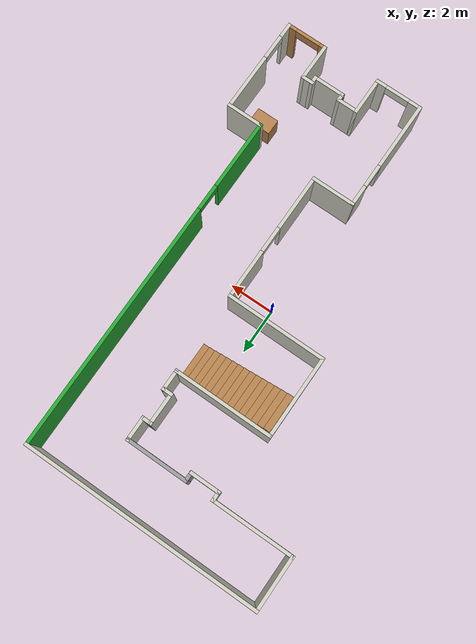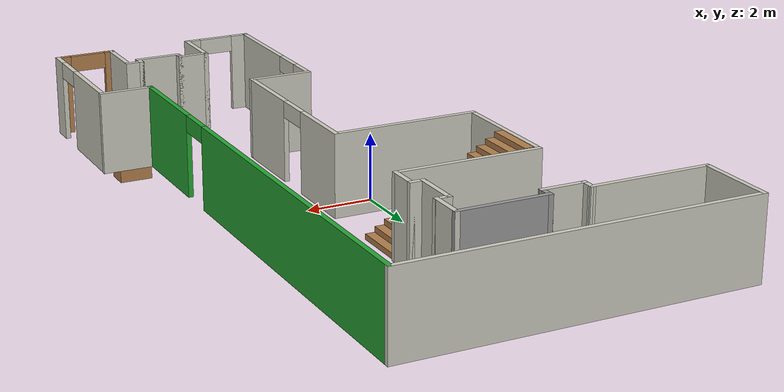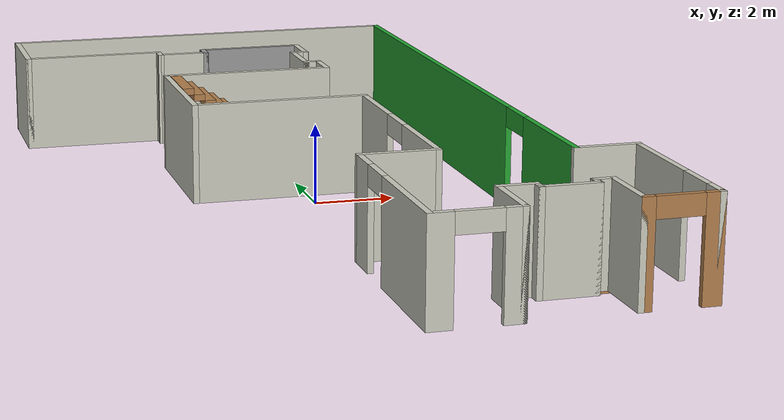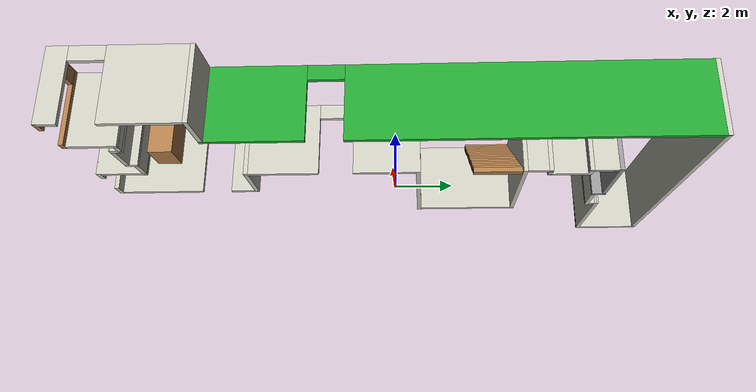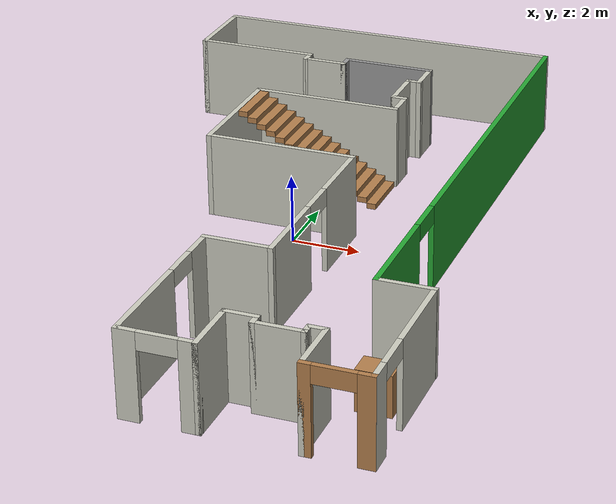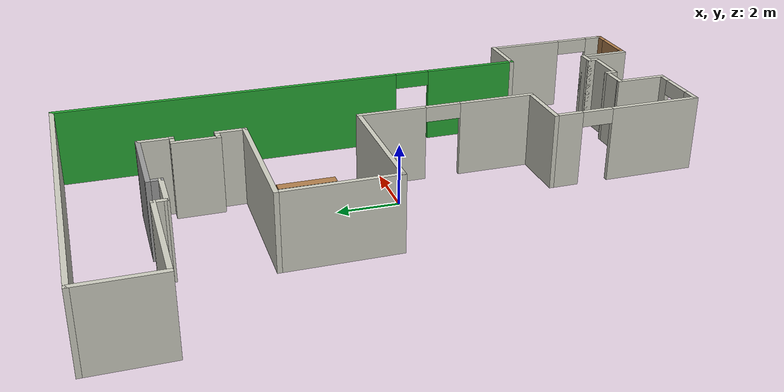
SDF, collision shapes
<?xml version='1.0'?>
<sdf version='1.6'>
  <model name='teknopark'>
    <link name='Stairs_0'>
      <pose frame=''>0 0 0 0 -0 0</pose>
      <inertial>
        <mass>1</mass>
        <pose frame=''>0 0 0 0 -0 0</pose>
        <inertia>
          <ixx>1</ixx>
          <ixy>0</ixy>
          <ixz>0</ixz>
          <iyy>1</iyy>
          <iyz>0</iyz>
          <izz>1</izz>
        </inertia>
      </inertial>
      <self_collide>0</self_collide>
      <kinematic>0</kinematic>
      <visual name='Stairs_0_Visual_1'>
        <pose frame=''>1.08758 3.51237 0.25 0 0 -1.5708</pose>
        <geometry>
          <box>
            <size>1.64 0.285333 0.166667</size>
          </box>
        </geometry>
        <material>
          <script>
            <uri>file://media/materials/scripts/gazebo.material</uri>
            <name>Gazebo/WoodFloor</name>
          </script>
          <ambient>1 1 1 1</ambient>
          <diffuse>0.7 0.7 0.7 1</diffuse>
          <specular>0.01 0.01 0.01 1</specular>
          <emissive>0 0 0 1</emissive>
          <shader type='vertex'>
            <normal_map>__default__</normal_map>
          </shader>
        </material>
        <cast_shadows>1</cast_shadows>
        <transparency>0</transparency>
      </visual>
      <visual name='Stairs_0_Visual_14'>
        <pose frame=''>-2.62175 3.51237 2.41667 0 0 -1.5708</pose>
        <geometry>
          <box>
            <size>1.64 0.285333 0.166667</size>
          </box>
        </geometry>
        <material>
          <script>
            <uri>file://media/materials/scripts/gazebo.material</uri>
            <name>Gazebo/WoodFloor</name>
          </script>
          <ambient>1 1 1 1</ambient>
          <diffuse>0.7 0.7 0.7 1</diffuse>
          <specular>0.01 0.01 0.01 1</specular>
          <emissive>0 0 0 1</emissive>
          <shader type='vertex'>
            <normal_map>__default__</normal_map>
          </shader>
        </material>
        <cast_shadows>1</cast_shadows>
        <transparency>0</transparency>
      </visual>
      <visual name='Stairs_0_Visual_2'>
        <pose frame=''>0.802247 3.51237 0.416667 0 0 -1.5708</pose>
        <geometry>
          <box>
            <size>1.64 0.285333 0.166667</size>
          </box>
        </geometry>
        <material>
          <script>
            <uri>file://media/materials/scripts/gazebo.material</uri>
            <name>Gazebo/WoodFloor</name>
          </script>
          <ambient>1 1 1 1</ambient>
          <diffuse>0.7 0.7 0.7 1</diffuse>
          <specular>0.01 0.01 0.01 1</specular>
          <emissive>0 0 0 1</emissive>
          <shader type='vertex'>
            <normal_map>__default__</normal_map>
          </shader>
        </material>
        <cast_shadows>1</cast_shadows>
        <transparency>0</transparency>
      </visual>
      <visual name='Stairs_0_Visual_13'>
        <pose frame=''>-2.33642 3.51237 2.25 0 0 -1.5708</pose>
        <geometry>
          <box>
            <size>1.64 0.285333 0.166667</size>
          </box>
        </geometry>
        <material>
          <script>
            <uri>file://media/materials/scripts/gazebo.material</uri>
            <name>Gazebo/WoodFloor</name>
          </script>
          <ambient>1 1 1 1</ambient>
          <diffuse>0.7 0.7 0.7 1</diffuse>
          <specular>0.01 0.01 0.01 1</specular>
          <emissive>0 0 0 1</emissive>
          <shader type='vertex'>
            <normal_map>__default__</normal_map>
          </shader>
        </material>
        <cast_shadows>1</cast_shadows>
        <transparency>0</transparency>
      </visual>
      <visual name='Stairs_0_Visual_7'>
        <pose frame=''>-0.62442 3.51237 1.25 0 0 -1.5708</pose>
        <geometry>
          <box>
            <size>1.64 0.285333 0.166667</size>
          </box>
        </geometry>
        <material>
          <script>
            <uri>file://media/materials/scripts/gazebo.material</uri>
            <name>Gazebo/WoodFloor</name>
          </script>
          <ambient>1 1 1 1</ambient>
          <diffuse>0.7 0.7 0.7 1</diffuse>
          <specular>0.01 0.01 0.01 1</specular>
          <emissive>0 0 0 1</emissive>
          <shader type='vertex'>
            <normal_map>__default__</normal_map>
          </shader>
        </material>
        <cast_shadows>1</cast_shadows>
        <transparency>0</transparency>
      </visual>
      <visual name='Stairs_0_Visual_4'>
        <pose frame=''>0.23158 3.51237 0.75 0 0 -1.5708</pose>
        <geometry>
          <box>
            <size>1.64 0.285333 0.166667</size>
          </box>
        </geometry>
        <material>
          <script>
            <uri>file://media/materials/scripts/gazebo.material</uri>
            <name>Gazebo/WoodFloor</name>
          </script>
          <ambient>1 1 1 1</ambient>
          <diffuse>0.7 0.7 0.7 1</diffuse>
          <specular>0.01 0.01 0.01 1</specular>
          <emissive>0 0 0 1</emissive>
          <shader type='vertex'>
            <normal_map>__default__</normal_map>
          </shader>
        </material>
        <cast_shadows>1</cast_shadows>
        <transparency>0</transparency>
      </visual>
      <visual name='Stairs_0_Visual_3'>
        <pose frame=''>0.516914 3.51237 0.583333 0 0 -1.5708</pose>
        <geometry>
          <box>
            <size>1.64 0.285333 0.166667</size>
          </box>
        </geometry>
        <material>
          <script>
            <uri>file://media/materials/scripts/gazebo.material</uri>
            <name>Gazebo/WoodFloor</name>
          </script>
          <ambient>1 1 1 1</ambient>
          <diffuse>0.7 0.7 0.7 1</diffuse>
          <specular>0.01 0.01 0.01 1</specular>
          <emissive>0 0 0 1</emissive>
          <shader type='vertex'>
            <normal_map>__default__</normal_map>
          </shader>
        </material>
        <cast_shadows>1</cast_shadows>
        <transparency>0</transparency>
      </visual>
      <visual name='Stairs_0_Visual_10'>
        <pose frame=''>-1.48042 3.51237 1.75 0 0 -1.5708</pose>
        <geometry>
          <box>
            <size>1.64 0.285333 0.166667</size>
          </box>
        </geometry>
        <material>
          <script>
            <uri>file://media/materials/scripts/gazebo.material</uri>
            <name>Gazebo/WoodFloor</name>
          </script>
          <ambient>1 1 1 1</ambient>
          <diffuse>0.7 0.7 0.7 1</diffuse>
          <specular>0.01 0.01 0.01 1</specular>
          <emissive>0 0 0 1</emissive>
          <shader type='vertex'>
            <normal_map>__default__</normal_map>
          </shader>
        </material>
        <cast_shadows>1</cast_shadows>
        <transparency>0</transparency>
      </visual>
      <visual name='Stairs_0_Visual_11'>
        <pose frame=''>-1.76575 3.51237 1.91667 0 0 -1.5708</pose>
        <geometry>
          <box>
            <size>1.64 0.285333 0.166667</size>
          </box>
        </geometry>
        <material>
          <script>
            <uri>file://media/materials/scripts/gazebo.material</uri>
            <name>Gazebo/WoodFloor</name>
          </script>
          <ambient>1 1 1 1</ambient>
          <diffuse>0.7 0.7 0.7 1</diffuse>
          <specular>0.01 0.01 0.01 1</specular>
          <emissive>0 0 0 1</emissive>
          <shader type='vertex'>
            <normal_map>__default__</normal_map>
          </shader>
        </material>
        <cast_shadows>1</cast_shadows>
        <transparency>0</transparency>
      </visual>
      <visual name='Stairs_0_Visual_12'>
        <pose frame=''>-2.05109 3.51237 2.08333 0 0 -1.5708</pose>
        <geometry>
          <box>
            <size>1.64 0.285333 0.166667</size>
          </box>
        </geometry>
        <material>
          <script>
            <uri>file://media/materials/scripts/gazebo.material</uri>
            <name>Gazebo/WoodFloor</name>
          </script>
          <ambient>1 1 1 1</ambient>
          <diffuse>0.7 0.7 0.7 1</diffuse>
          <specular>0.01 0.01 0.01 1</specular>
          <emissive>0 0 0 1</emissive>
          <shader type='vertex'>
            <normal_map>__default__</normal_map>
          </shader>
        </material>
        <cast_shadows>1</cast_shadows>
        <transparency>0</transparency>
      </visual>
      <visual name='Stairs_0_Visual_9'>
        <pose frame=''>-1.19509 3.51237 1.58333 0 0 -1.5708</pose>
        <geometry>
          <box>
            <size>1.64 0.285333 0.166667</size>
          </box>
        </geometry>
        <material>
          <script>
            <uri>file://media/materials/scripts/gazebo.material</uri>
            <name>Gazebo/WoodFloor</name>
          </script>
          <ambient>1 1 1 1</ambient>
          <diffuse>0.7 0.7 0.7 1</diffuse>
          <specular>0.01 0.01 0.01 1</specular>
          <emissive>0 0 0 1</emissive>
          <shader type='vertex'>
            <normal_map>__default__</normal_map>
          </shader>
        </material>
        <cast_shadows>1</cast_shadows>
        <transparency>0</transparency>
      </visual>
      <visual name='Stairs_0_Visual_5'>
        <pose frame=''>-0.053754 3.51237 0.916667 0 0 -1.5708</pose>
        <geometry>
          <box>
            <size>1.64 0.285333 0.166667</size>
          </box>
        </geometry>
        <material>
          <script>
            <uri>file://media/materials/scripts/gazebo.material</uri>
            <name>Gazebo/WoodFloor</name>
          </script>
          <ambient>1 1 1 1</ambient>
          <diffuse>0.7 0.7 0.7 1</diffuse>
          <specular>0.01 0.01 0.01 1</specular>
          <emissive>0 0 0 1</emissive>
          <shader type='vertex'>
            <normal_map>__default__</normal_map>
          </shader>
        </material>
        <cast_shadows>1</cast_shadows>
        <transparency>0</transparency>
      </visual>
      <visual name='Stairs_0_Visual_6'>
        <pose frame=''>-0.339086 3.51237 1.08333 0 0 -1.5708</pose>
        <geometry>
          <box>
            <size>1.64 0.285333 0.166667</size>
          </box>
        </geometry>
        <material>
          <script>
            <uri>file://media/materials/scripts/gazebo.material</uri>
            <name>Gazebo/WoodFloor</name>
          </script>
          <ambient>1 1 1 1</ambient>
          <diffuse>0.7 0.7 0.7 1</diffuse>
          <specular>0.01 0.01 0.01 1</specular>
          <emissive>0 0 0 1</emissive>
          <shader type='vertex'>
            <normal_map>__default__</normal_map>
          </shader>
        </material>
        <cast_shadows>1</cast_shadows>
        <transparency>0</transparency>
      </visual>
      <visual name='Stairs_0_Visual_0'>
        <pose frame=''>1.37291 3.51237 0.083333 0 0 -1.5708</pose>
        <geometry>
          <box>
            <size>1.64 0.285333 0.166667</size>
          </box>
        </geometry>
        <material>
          <script>
            <uri>file://media/materials/scripts/gazebo.material</uri>
            <name>Gazebo/WoodFloor</name>
          </script>
          <ambient>1 1 1 1</ambient>
          <diffuse>0.7 0.7 0.7 1</diffuse>
          <specular>0.01 0.01 0.01 1</specular>
          <emissive>0 0 0 1</emissive>
          <shader type='vertex'>
            <normal_map>__default__</normal_map>
          </shader>
        </material>
        <cast_shadows>1</cast_shadows>
        <transparency>0</transparency>
      </visual>
      <visual name='Stairs_0_Visual_8'>
        <pose frame=''>-0.909754 3.51237 1.41667 0 0 -1.5708</pose>
        <geometry>
          <box>
            <size>1.64 0.285333 0.166667</size>
          </box>
        </geometry>
        <material>
          <script>
            <uri>file://media/materials/scripts/gazebo.material</uri>
            <name>Gazebo/WoodFloor</name>
          </script>
          <ambient>1 1 1 1</ambient>
          <diffuse>0.7 0.7 0.7 1</diffuse>
          <specular>0.01 0.01 0.01 1</specular>
          <emissive>0 0 0 1</emissive>
          <shader type='vertex'>
            <normal_map>__default__</normal_map>
          </shader>
        </material>
        <cast_shadows>1</cast_shadows>
        <transparency>0</transparency>
      </visual>
      <collision name='Stairs_0_Collision_11'>
        <laser_retro>0</laser_retro>
        <max_contacts>10</max_contacts>
        <pose frame=''>-1.76575 3.51237 1.91667 0 0 -1.5708</pose>
        <geometry>
          <box>
            <size>1.64 0.285333 0.166667</size>
          </box>
        </geometry>
        <surface>
          <friction>
            <ode>
              <mu>1</mu>
              <mu2>1</mu2>
              <fdir1>0 0 0</fdir1>
              <slip1>0</slip1>
              <slip2>0</slip2>
            </ode>
            <torsional>
              <coefficient>1</coefficient>
              <patch_radius>0</patch_radius>
              <surface_radius>0</surface_radius>
              <use_patch_radius>1</use_patch_radius>
              <ode>
                <slip>0</slip>
              </ode>
            </torsional>
          </friction>
          <bounce>
            <restitution_coefficient>0</restitution_coefficient>
            <threshold>1e+06</threshold>
          </bounce>
          <contact>
            <collide_without_contact>0</collide_without_contact>
            <collide_without_contact_bitmask>1</collide_without_contact_bitmask>
            <collide_bitmask>1</collide_bitmask>
            <ode>
              <soft_cfm>0</soft_cfm>
              <soft_erp>0.2</soft_erp>
              <kp>1e+13</kp>
              <kd>1</kd>
              <max_vel>0.01</max_vel>
              <min_depth>0</min_depth>
            </ode>
            <bullet>
              <split_impulse>1</split_impulse>
              <split_impulse_penetration_threshold>-0.01</split_impulse_penetration_threshold>
              <soft_cfm>0</soft_cfm>
              <soft_erp>0.2</soft_erp>
              <kp>1e+13</kp>
              <kd>1</kd>
            </bullet>
          </contact>
        </surface>
      </collision>
      <collision name='Stairs_0_Collision_0'>
        <laser_retro>0</laser_retro>
        <max_contacts>10</max_contacts>
        <pose frame=''>1.37291 3.51237 0.083333 0 0 -1.5708</pose>
        <geometry>
          <box>
            <size>1.64 0.285333 0.166667</size>
          </box>
        </geometry>
        <surface>
          <friction>
            <ode>
              <mu>1</mu>
              <mu2>1</mu2>
              <fdir1>0 0 0</fdir1>
              <slip1>0</slip1>
              <slip2>0</slip2>
            </ode>
            <torsional>
              <coefficient>1</coefficient>
              <patch_radius>0</patch_radius>
              <surface_radius>0</surface_radius>
              <use_patch_radius>1</use_patch_radius>
              <ode>
                <slip>0</slip>
              </ode>
            </torsional>
          </friction>
          <bounce>
            <restitution_coefficient>0</restitution_coefficient>
            <threshold>1e+06</threshold>
          </bounce>
          <contact>
            <collide_without_contact>0</collide_without_contact>
            <collide_without_contact_bitmask>1</collide_without_contact_bitmask>
            <collide_bitmask>1</collide_bitmask>
            <ode>
              <soft_cfm>0</soft_cfm>
              <soft_erp>0.2</soft_erp>
              <kp>1e+13</kp>
              <kd>1</kd>
              <max_vel>0.01</max_vel>
              <min_depth>0</min_depth>
            </ode>
            <bullet>
              <split_impulse>1</split_impulse>
              <split_impulse_penetration_threshold>-0.01</split_impulse_penetration_threshold>
              <soft_cfm>0</soft_cfm>
              <soft_erp>0.2</soft_erp>
              <kp>1e+13</kp>
              <kd>1</kd>
            </bullet>
          </contact>
        </surface>
      </collision>
      <collision name='Stairs_0_Collision_1'>
        <laser_retro>0</laser_retro>
        <max_contacts>10</max_contacts>
        <pose frame=''>1.08758 3.51237 0.25 0 0 -1.5708</pose>
        <geometry>
          <box>
            <size>1.64 0.285333 0.166667</size>
          </box>
        </geometry>
        <surface>
          <friction>
            <ode>
              <mu>1</mu>
              <mu2>1</mu2>
              <fdir1>0 0 0</fdir1>
              <slip1>0</slip1>
              <slip2>0</slip2>
            </ode>
            <torsional>
              <coefficient>1</coefficient>
              <patch_radius>0</patch_radius>
              <surface_radius>0</surface_radius>
              <use_patch_radius>1</use_patch_radius>
              <ode>
                <slip>0</slip>
              </ode>
            </torsional>
          </friction>
          <bounce>
            <restitution_coefficient>0</restitution_coefficient>
            <threshold>1e+06</threshold>
          </bounce>
          <contact>
            <collide_without_contact>0</collide_without_contact>
            <collide_without_contact_bitmask>1</collide_without_contact_bitmask>
            <collide_bitmask>1</collide_bitmask>
            <ode>
              <soft_cfm>0</soft_cfm>
              <soft_erp>0.2</soft_erp>
              <kp>1e+13</kp>
              <kd>1</kd>
              <max_vel>0.01</max_vel>
              <min_depth>0</min_depth>
            </ode>
            <bullet>
              <split_impulse>1</split_impulse>
              <split_impulse_penetration_threshold>-0.01</split_impulse_penetration_threshold>
              <soft_cfm>0</soft_cfm>
              <soft_erp>0.2</soft_erp>
              <kp>1e+13</kp>
              <kd>1</kd>
            </bullet>
          </contact>
        </surface>
      </collision>
      <collision name='Stairs_0_Collision_7'>
        <laser_retro>0</laser_retro>
        <max_contacts>10</max_contacts>
        <pose frame=''>-0.62442 3.51237 1.25 0 0 -1.5708</pose>
        <geometry>
          <box>
            <size>1.64 0.285333 0.166667</size>
          </box>
        </geometry>
        <surface>
          <friction>
            <ode>
              <mu>1</mu>
              <mu2>1</mu2>
              <fdir1>0 0 0</fdir1>
              <slip1>0</slip1>
              <slip2>0</slip2>
            </ode>
            <torsional>
              <coefficient>1</coefficient>
              <patch_radius>0</patch_radius>
              <surface_radius>0</surface_radius>
              <use_patch_radius>1</use_patch_radius>
              <ode>
                <slip>0</slip>
              </ode>
            </torsional>
          </friction>
          <bounce>
            <restitution_coefficient>0</restitution_coefficient>
            <threshold>1e+06</threshold>
          </bounce>
          <contact>
            <collide_without_contact>0</collide_without_contact>
            <collide_without_contact_bitmask>1</collide_without_contact_bitmask>
            <collide_bitmask>1</collide_bitmask>
            <ode>
              <soft_cfm>0</soft_cfm>
              <soft_erp>0.2</soft_erp>
              <kp>1e+13</kp>
              <kd>1</kd>
              <max_vel>0.01</max_vel>
              <min_depth>0</min_depth>
            </ode>
            <bullet>
              <split_impulse>1</split_impulse>
              <split_impulse_penetration_threshold>-0.01</split_impulse_penetration_threshold>
              <soft_cfm>0</soft_cfm>
              <soft_erp>0.2</soft_erp>
              <kp>1e+13</kp>
              <kd>1</kd>
            </bullet>
          </contact>
        </surface>
      </collision>
      <collision name='Stairs_0_Collision_8'>
        <laser_retro>0</laser_retro>
        <max_contacts>10</max_contacts>
        <pose frame=''>-0.909754 3.51237 1.41667 0 0 -1.5708</pose>
        <geometry>
          <box>
            <size>1.64 0.285333 0.166667</size>
          </box>
        </geometry>
        <surface>
          <friction>
            <ode>
              <mu>1</mu>
              <mu2>1</mu2>
              <fdir1>0 0 0</fdir1>
              <slip1>0</slip1>
              <slip2>0</slip2>
            </ode>
            <torsional>
              <coefficient>1</coefficient>
              <patch_radius>0</patch_radius>
              <surface_radius>0</surface_radius>
              <use_patch_radius>1</use_patch_radius>
              <ode>
                <slip>0</slip>
              </ode>
            </torsional>
          </friction>
          <bounce>
            <restitution_coefficient>0</restitution_coefficient>
            <threshold>1e+06</threshold>
          </bounce>
          <contact>
            <collide_without_contact>0</collide_without_contact>
            <collide_without_contact_bitmask>1</collide_without_contact_bitmask>
            <collide_bitmask>1</collide_bitmask>
            <ode>
              <soft_cfm>0</soft_cfm>
              <soft_erp>0.2</soft_erp>
              <kp>1e+13</kp>
              <kd>1</kd>
              <max_vel>0.01</max_vel>
              <min_depth>0</min_depth>
            </ode>
            <bullet>
              <split_impulse>1</split_impulse>
              <split_impulse_penetration_threshold>-0.01</split_impulse_penetration_threshold>
              <soft_cfm>0</soft_cfm>
              <soft_erp>0.2</soft_erp>
              <kp>1e+13</kp>
              <kd>1</kd>
            </bullet>
          </contact>
        </surface>
      </collision>
      <collision name='Stairs_0_Collision_12'>
        <laser_retro>0</laser_retro>
        <max_contacts>10</max_contacts>
        <pose frame=''>-2.05109 3.51237 2.08333 0 0 -1.5708</pose>
        <geometry>
          <box>
            <size>1.64 0.285333 0.166667</size>
          </box>
        </geometry>
        <surface>
          <friction>
            <ode>
              <mu>1</mu>
              <mu2>1</mu2>
              <fdir1>0 0 0</fdir1>
              <slip1>0</slip1>
              <slip2>0</slip2>
            </ode>
            <torsional>
              <coefficient>1</coefficient>
              <patch_radius>0</patch_radius>
              <surface_radius>0</surface_radius>
              <use_patch_radius>1</use_patch_radius>
              <ode>
                <slip>0</slip>
              </ode>
            </torsional>
          </friction>
          <bounce>
            <restitution_coefficient>0</restitution_coefficient>
            <threshold>1e+06</threshold>
          </bounce>
          <contact>
            <collide_without_contact>0</collide_without_contact>
            <collide_without_contact_bitmask>1</collide_without_contact_bitmask>
            <collide_bitmask>1</collide_bitmask>
            <ode>
              <soft_cfm>0</soft_cfm>
              <soft_erp>0.2</soft_erp>
              <kp>1e+13</kp>
              <kd>1</kd>
              <max_vel>0.01</max_vel>
              <min_depth>0</min_depth>
            </ode>
            <bullet>
              <split_impulse>1</split_impulse>
              <split_impulse_penetration_threshold>-0.01</split_impulse_penetration_threshold>
              <soft_cfm>0</soft_cfm>
              <soft_erp>0.2</soft_erp>
              <kp>1e+13</kp>
              <kd>1</kd>
            </bullet>
          </contact>
        </surface>
      </collision>
      <collision name='Stairs_0_Collision_3'>
        <laser_retro>0</laser_retro>
        <max_contacts>10</max_contacts>
        <pose frame=''>0.516914 3.51237 0.583333 0 0 -1.5708</pose>
        <geometry>
          <box>
            <size>1.64 0.285333 0.166667</size>
          </box>
        </geometry>
        <surface>
          <friction>
            <ode>
              <mu>1</mu>
              <mu2>1</mu2>
              <fdir1>0 0 0</fdir1>
              <slip1>0</slip1>
              <slip2>0</slip2>
            </ode>
            <torsional>
              <coefficient>1</coefficient>
              <patch_radius>0</patch_radius>
              <surface_radius>0</surface_radius>
              <use_patch_radius>1</use_patch_radius>
              <ode>
                <slip>0</slip>
              </ode>
            </torsional>
          </friction>
          <bounce>
            <restitution_coefficient>0</restitution_coefficient>
            <threshold>1e+06</threshold>
          </bounce>
          <contact>
            <collide_without_contact>0</collide_without_contact>
            <collide_without_contact_bitmask>1</collide_without_contact_bitmask>
            <collide_bitmask>1</collide_bitmask>
            <ode>
              <soft_cfm>0</soft_cfm>
              <soft_erp>0.2</soft_erp>
              <kp>1e+13</kp>
              <kd>1</kd>
              <max_vel>0.01</max_vel>
              <min_depth>0</min_depth>
            </ode>
            <bullet>
              <split_impulse>1</split_impulse>
              <split_impulse_penetration_threshold>-0.01</split_impulse_penetration_threshold>
              <soft_cfm>0</soft_cfm>
              <soft_erp>0.2</soft_erp>
              <kp>1e+13</kp>
              <kd>1</kd>
            </bullet>
          </contact>
        </surface>
      </collision>
      <collision name='Stairs_0_Collision_2'>
        <laser_retro>0</laser_retro>
        <max_contacts>10</max_contacts>
        <pose frame=''>0.802247 3.51237 0.416667 0 0 -1.5708</pose>
        <geometry>
          <box>
            <size>1.64 0.285333 0.166667</size>
          </box>
        </geometry>
        <surface>
          <friction>
            <ode>
              <mu>1</mu>
              <mu2>1</mu2>
              <fdir1>0 0 0</fdir1>
              <slip1>0</slip1>
              <slip2>0</slip2>
            </ode>
            <torsional>
              <coefficient>1</coefficient>
              <patch_radius>0</patch_radius>
              <surface_radius>0</surface_radius>
              <use_patch_radius>1</use_patch_radius>
              <ode>
                <slip>0</slip>
              </ode>
            </torsional>
          </friction>
          <bounce>
            <restitution_coefficient>0</restitution_coefficient>
            <threshold>1e+06</threshold>
          </bounce>
          <contact>
            <collide_without_contact>0</collide_without_contact>
            <collide_without_contact_bitmask>1</collide_without_contact_bitmask>
            <collide_bitmask>1</collide_bitmask>
            <ode>
              <soft_cfm>0</soft_cfm>
              <soft_erp>0.2</soft_erp>
              <kp>1e+13</kp>
              <kd>1</kd>
              <max_vel>0.01</max_vel>
              <min_depth>0</min_depth>
            </ode>
            <bullet>
              <split_impulse>1</split_impulse>
              <split_impulse_penetration_threshold>-0.01</split_impulse_penetration_threshold>
              <soft_cfm>0</soft_cfm>
              <soft_erp>0.2</soft_erp>
              <kp>1e+13</kp>
              <kd>1</kd>
            </bullet>
          </contact>
        </surface>
      </collision>
      <collision name='Stairs_0_Collision_13'>
        <laser_retro>0</laser_retro>
        <max_contacts>10</max_contacts>
        <pose frame=''>-2.33642 3.51237 2.25 0 0 -1.5708</pose>
        <geometry>
          <box>
            <size>1.64 0.285333 0.166667</size>
          </box>
        </geometry>
        <surface>
          <friction>
            <ode>
              <mu>1</mu>
              <mu2>1</mu2>
              <fdir1>0 0 0</fdir1>
              <slip1>0</slip1>
              <slip2>0</slip2>
            </ode>
            <torsional>
              <coefficient>1</coefficient>
              <patch_radius>0</patch_radius>
              <surface_radius>0</surface_radius>
              <use_patch_radius>1</use_patch_radius>
              <ode>
                <slip>0</slip>
              </ode>
            </torsional>
          </friction>
          <bounce>
            <restitution_coefficient>0</restitution_coefficient>
            <threshold>1e+06</threshold>
          </bounce>
          <contact>
            <collide_without_contact>0</collide_without_contact>
            <collide_without_contact_bitmask>1</collide_without_contact_bitmask>
            <collide_bitmask>1</collide_bitmask>
            <ode>
              <soft_cfm>0</soft_cfm>
              <soft_erp>0.2</soft_erp>
              <kp>1e+13</kp>
              <kd>1</kd>
              <max_vel>0.01</max_vel>
              <min_depth>0</min_depth>
            </ode>
            <bullet>
              <split_impulse>1</split_impulse>
              <split_impulse_penetration_threshold>-0.01</split_impulse_penetration_threshold>
              <soft_cfm>0</soft_cfm>
              <soft_erp>0.2</soft_erp>
              <kp>1e+13</kp>
              <kd>1</kd>
            </bullet>
          </contact>
        </surface>
      </collision>
      <collision name='Stairs_0_Collision_14'>
        <laser_retro>0</laser_retro>
        <max_contacts>10</max_contacts>
        <pose frame=''>-2.62175 3.51237 2.41667 0 0 -1.5708</pose>
        <geometry>
          <box>
            <size>1.64 0.285333 0.166667</size>
          </box>
        </geometry>
        <surface>
          <friction>
            <ode>
              <mu>1</mu>
              <mu2>1</mu2>
              <fdir1>0 0 0</fdir1>
              <slip1>0</slip1>
              <slip2>0</slip2>
            </ode>
            <torsional>
              <coefficient>1</coefficient>
              <patch_radius>0</patch_radius>
              <surface_radius>0</surface_radius>
              <use_patch_radius>1</use_patch_radius>
              <ode>
                <slip>0</slip>
              </ode>
            </torsional>
          </friction>
          <bounce>
            <restitution_coefficient>0</restitution_coefficient>
            <threshold>1e+06</threshold>
          </bounce>
          <contact>
            <collide_without_contact>0</collide_without_contact>
            <collide_without_contact_bitmask>1</collide_without_contact_bitmask>
            <collide_bitmask>1</collide_bitmask>
            <ode>
              <soft_cfm>0</soft_cfm>
              <soft_erp>0.2</soft_erp>
              <kp>1e+13</kp>
              <kd>1</kd>
              <max_vel>0.01</max_vel>
              <min_depth>0</min_depth>
            </ode>
            <bullet>
              <split_impulse>1</split_impulse>
              <split_impulse_penetration_threshold>-0.01</split_impulse_penetration_threshold>
              <soft_cfm>0</soft_cfm>
              <soft_erp>0.2</soft_erp>
              <kp>1e+13</kp>
              <kd>1</kd>
            </bullet>
          </contact>
        </surface>
      </collision>
      <collision name='Stairs_0_Collision_5'>
        <laser_retro>0</laser_retro>
        <max_contacts>10</max_contacts>
        <pose frame=''>-0.053754 3.51237 0.916667 0 0 -1.5708</pose>
        <geometry>
          <box>
            <size>1.64 0.285333 0.166667</size>
          </box>
        </geometry>
        <surface>
          <friction>
            <ode>
              <mu>1</mu>
              <mu2>1</mu2>
              <fdir1>0 0 0</fdir1>
              <slip1>0</slip1>
              <slip2>0</slip2>
            </ode>
            <torsional>
              <coefficient>1</coefficient>
              <patch_radius>0</patch_radius>
              <surface_radius>0</surface_radius>
              <use_patch_radius>1</use_patch_radius>
              <ode>
                <slip>0</slip>
              </ode>
            </torsional>
          </friction>
          <bounce>
            <restitution_coefficient>0</restitution_coefficient>
            <threshold>1e+06</threshold>
          </bounce>
          <contact>
            <collide_without_contact>0</collide_without_contact>
            <collide_without_contact_bitmask>1</collide_without_contact_bitmask>
            <collide_bitmask>1</collide_bitmask>
            <ode>
              <soft_cfm>0</soft_cfm>
              <soft_erp>0.2</soft_erp>
              <kp>1e+13</kp>
              <kd>1</kd>
              <max_vel>0.01</max_vel>
              <min_depth>0</min_depth>
            </ode>
            <bullet>
              <split_impulse>1</split_impulse>
              <split_impulse_penetration_threshold>-0.01</split_impulse_penetration_threshold>
              <soft_cfm>0</soft_cfm>
              <soft_erp>0.2</soft_erp>
              <kp>1e+13</kp>
              <kd>1</kd>
            </bullet>
          </contact>
        </surface>
      </collision>
      <collision name='Stairs_0_Collision_6'>
        <laser_retro>0</laser_retro>
        <max_contacts>10</max_contacts>
        <pose frame=''>-0.339086 3.51237 1.08333 0 0 -1.5708</pose>
        <geometry>
          <box>
            <size>1.64 0.285333 0.166667</size>
          </box>
        </geometry>
        <surface>
          <friction>
            <ode>
              <mu>1</mu>
              <mu2>1</mu2>
              <fdir1>0 0 0</fdir1>
              <slip1>0</slip1>
              <slip2>0</slip2>
            </ode>
            <torsional>
              <coefficient>1</coefficient>
              <patch_radius>0</patch_radius>
              <surface_radius>0</surface_radius>
              <use_patch_radius>1</use_patch_radius>
              <ode>
                <slip>0</slip>
              </ode>
            </torsional>
          </friction>
          <bounce>
            <restitution_coefficient>0</restitution_coefficient>
            <threshold>1e+06</threshold>
          </bounce>
          <contact>
            <collide_without_contact>0</collide_without_contact>
            <collide_without_contact_bitmask>1</collide_without_contact_bitmask>
            <collide_bitmask>1</collide_bitmask>
            <ode>
              <soft_cfm>0</soft_cfm>
              <soft_erp>0.2</soft_erp>
              <kp>1e+13</kp>
              <kd>1</kd>
              <max_vel>0.01</max_vel>
              <min_depth>0</min_depth>
            </ode>
            <bullet>
              <split_impulse>1</split_impulse>
              <split_impulse_penetration_threshold>-0.01</split_impulse_penetration_threshold>
              <soft_cfm>0</soft_cfm>
              <soft_erp>0.2</soft_erp>
              <kp>1e+13</kp>
              <kd>1</kd>
            </bullet>
          </contact>
        </surface>
      </collision>
      <collision name='Stairs_0_Collision_10'>
        <laser_retro>0</laser_retro>
        <max_contacts>10</max_contacts>
        <pose frame=''>-1.48042 3.51237 1.75 0 0 -1.5708</pose>
        <geometry>
          <box>
            <size>1.64 0.285333 0.166667</size>
          </box>
        </geometry>
        <surface>
          <friction>
            <ode>
              <mu>1</mu>
              <mu2>1</mu2>
              <fdir1>0 0 0</fdir1>
              <slip1>0</slip1>
              <slip2>0</slip2>
            </ode>
            <torsional>
              <coefficient>1</coefficient>
              <patch_radius>0</patch_radius>
              <surface_radius>0</surface_radius>
              <use_patch_radius>1</use_patch_radius>
              <ode>
                <slip>0</slip>
              </ode>
            </torsional>
          </friction>
          <bounce>
            <restitution_coefficient>0</restitution_coefficient>
            <threshold>1e+06</threshold>
          </bounce>
          <contact>
            <collide_without_contact>0</collide_without_contact>
            <collide_without_contact_bitmask>1</collide_without_contact_bitmask>
            <collide_bitmask>1</collide_bitmask>
            <ode>
              <soft_cfm>0</soft_cfm>
              <soft_erp>0.2</soft_erp>
              <kp>1e+13</kp>
              <kd>1</kd>
              <max_vel>0.01</max_vel>
              <min_depth>0</min_depth>
            </ode>
            <bullet>
              <split_impulse>1</split_impulse>
              <split_impulse_penetration_threshold>-0.01</split_impulse_penetration_threshold>
              <soft_cfm>0</soft_cfm>
              <soft_erp>0.2</soft_erp>
              <kp>1e+13</kp>
              <kd>1</kd>
            </bullet>
          </contact>
        </surface>
      </collision>
      <collision name='Stairs_0_Collision_9'>
        <laser_retro>0</laser_retro>
        <max_contacts>10</max_contacts>
        <pose frame=''>-1.19509 3.51237 1.58333 0 0 -1.5708</pose>
        <geometry>
          <box>
            <size>1.64 0.285333 0.166667</size>
          </box>
        </geometry>
        <surface>
          <friction>
            <ode>
              <mu>1</mu>
              <mu2>1</mu2>
              <fdir1>0 0 0</fdir1>
              <slip1>0</slip1>
              <slip2>0</slip2>
            </ode>
            <torsional>
              <coefficient>1</coefficient>
              <patch_radius>0</patch_radius>
              <surface_radius>0</surface_radius>
              <use_patch_radius>1</use_patch_radius>
              <ode>
                <slip>0</slip>
              </ode>
            </torsional>
          </friction>
          <bounce>
            <restitution_coefficient>0</restitution_coefficient>
            <threshold>1e+06</threshold>
          </bounce>
          <contact>
            <collide_without_contact>0</collide_without_contact>
            <collide_without_contact_bitmask>1</collide_without_contact_bitmask>
            <collide_bitmask>1</collide_bitmask>
            <ode>
              <soft_cfm>0</soft_cfm>
              <soft_erp>0.2</soft_erp>
              <kp>1e+13</kp>
              <kd>1</kd>
              <max_vel>0.01</max_vel>
              <min_depth>0</min_depth>
            </ode>
            <bullet>
              <split_impulse>1</split_impulse>
              <split_impulse_penetration_threshold>-0.01</split_impulse_penetration_threshold>
              <soft_cfm>0</soft_cfm>
              <soft_erp>0.2</soft_erp>
              <kp>1e+13</kp>
              <kd>1</kd>
            </bullet>
          </contact>
        </surface>
      </collision>
      <collision name='Stairs_0_Collision_4'>
        <laser_retro>0</laser_retro>
        <max_contacts>10</max_contacts>
        <pose frame=''>0.23158 3.51237 0.75 0 0 -1.5708</pose>
        <geometry>
          <box>
            <size>1.64 0.285333 0.166667</size>
          </box>
        </geometry>
        <surface>
          <friction>
            <ode>
              <mu>1</mu>
              <mu2>1</mu2>
              <fdir1>0 0 0</fdir1>
              <slip1>0</slip1>
              <slip2>0</slip2>
            </ode>
            <torsional>
              <coefficient>1</coefficient>
              <patch_radius>0</patch_radius>
              <surface_radius>0</surface_radius>
              <use_patch_radius>1</use_patch_radius>
              <ode>
                <slip>0</slip>
              </ode>
            </torsional>
          </friction>
          <bounce>
            <restitution_coefficient>0</restitution_coefficient>
            <threshold>1e+06</threshold>
          </bounce>
          <contact>
            <collide_without_contact>0</collide_without_contact>
            <collide_without_contact_bitmask>1</collide_without_contact_bitmask>
            <collide_bitmask>1</collide_bitmask>
            <ode>
              <soft_cfm>0</soft_cfm>
              <soft_erp>0.2</soft_erp>
              <kp>1e+13</kp>
              <kd>1</kd>
              <max_vel>0.01</max_vel>
              <min_depth>0</min_depth>
            </ode>
            <bullet>
              <split_impulse>1</split_impulse>
              <split_impulse_penetration_threshold>-0.01</split_impulse_penetration_threshold>
              <soft_cfm>0</soft_cfm>
              <soft_erp>0.2</soft_erp>
              <kp>1e+13</kp>
              <kd>1</kd>
            </bullet>
          </contact>
        </surface>
      </collision>
    </link>
    <link name='Wall_17'>
      <pose frame=''>5.29992 -5.6595 0 0 -0 3.14159</pose>
      <inertial>
        <mass>1</mass>
        <pose frame=''>0 0 0 0 -0 0</pose>
        <inertia>
          <ixx>1</ixx>
          <ixy>0</ixy>
          <ixz>0</ixz>
          <iyy>1</iyy>
          <iyz>0</iyz>
          <izz>1</izz>
        </inertia>
      </inertial>
      <self_collide>0</self_collide>
      <kinematic>0</kinematic>
      <visual name='Wall_17_Visual'>
        <pose frame=''>0 0 1.25 0 -0 0</pose>
        <geometry>
          <box>
            <size>1.668 0.15 2.5</size>
          </box>
        </geometry>
        <material>
          <script>
            <uri>file://media/materials/scripts/gazebo.material</uri>
            <name>Gazebo/PaintedWall</name>
          </script>
          <ambient>1 1 1 1</ambient>
          <diffuse>0.7 0.7 0.7 1</diffuse>
          <specular>0.01 0.01 0.01 1</specular>
          <emissive>0 0 0 1</emissive>
          <shader type='vertex'>
            <normal_map>__default__</normal_map>
          </shader>
        </material>
        <cast_shadows>1</cast_shadows>
        <transparency>0</transparency>
      </visual>
      <visual name='ModelPreview_3::Wall_17::visual_1'>
        <pose frame=''>0 0 1.25 0 -0 0</pose>
        <geometry>
          <box>
            <size>1.668 0.15 2.5</size>
          </box>
        </geometry>
        <material>
          <script>
            <uri>file://media/materials/scripts/gazebo.material</uri>
            <name>Gazebo/Grey</name>
          </script>
          <ambient>1 1 1 1</ambient>
          <diffuse>0.7 0.7 0.7 1</diffuse>
          <specular>0.01 0.01 0.01 1</specular>
          <emissive>0 0 0 1</emissive>
          <shader type='vertex'>
            <normal_map>__default__</normal_map>
          </shader>
        </material>
        <cast_shadows>1</cast_shadows>
        <transparency>0</transparency>
      </visual>
      <collision name='Wall_17_Collision'>
        <laser_retro>0</laser_retro>
        <max_contacts>10</max_contacts>
        <pose frame=''>0 0 1.25 0 -0 0</pose>
        <geometry>
          <box>
            <size>1.668 0.15 2.5</size>
          </box>
        </geometry>
        <surface>
          <friction>
            <ode>
              <mu>1</mu>
              <mu2>1</mu2>
              <fdir1>0 0 0</fdir1>
              <slip1>0</slip1>
              <slip2>0</slip2>
            </ode>
            <torsional>
              <coefficient>1</coefficient>
              <patch_radius>0</patch_radius>
              <surface_radius>0</surface_radius>
              <use_patch_radius>1</use_patch_radius>
              <ode>
                <slip>0</slip>
              </ode>
            </torsional>
          </friction>
          <bounce>
            <restitution_coefficient>0</restitution_coefficient>
            <threshold>1e+06</threshold>
          </bounce>
          <contact>
            <collide_without_contact>0</collide_without_contact>
            <collide_without_contact_bitmask>1</collide_without_contact_bitmask>
            <collide_bitmask>1</collide_bitmask>
            <ode>
              <soft_cfm>0</soft_cfm>
              <soft_erp>0.2</soft_erp>
              <kp>1e+13</kp>
              <kd>1</kd>
              <max_vel>0.01</max_vel>
              <min_depth>0</min_depth>
            </ode>
            <bullet>
              <split_impulse>1</split_impulse>
              <split_impulse_penetration_threshold>-0.01</split_impulse_penetration_threshold>
              <soft_cfm>0</soft_cfm>
              <soft_erp>0.2</soft_erp>
              <kp>1e+13</kp>
              <kd>1</kd>
            </bullet>
          </contact>
        </surface>
      </collision>
    </link>
    <link name='Wall_20'>
      <pose frame=''>4.54092 2.156 0 0 -0 1.5708</pose>
      <inertial>
        <mass>1</mass>
        <pose frame=''>0 0 0 0 -0 0</pose>
        <inertia>
          <ixx>1</ixx>
          <ixy>0</ixy>
          <ixz>0</ixz>
          <iyy>1</iyy>
          <iyz>0</iyz>
          <izz>1</izz>
        </inertia>
      </inertial>
      <self_collide>0</self_collide>
      <kinematic>0</kinematic>
      <visual name='Wall_20_Door'>
        <pose frame=''>-4.10646 0 0 0 -0 0</pose>
        <geometry>
          <mesh>
            <uri>model://teknopark/meshes/Door_Component_BI3.dae</uri>
            <scale>1.2 1 1</scale>
          </mesh>
        </geometry>
        <cast_shadows>1</cast_shadows>
        <transparency>0</transparency>
        <material>
          <ambient>0 1 0 1</ambient>
          <diffuse>0 1 0 1</diffuse>
          <specular>0.1 0.1 0.1 1</specular>
          <emissive>0 0 0 1</emissive>
          <script>
            <name>Gazebo/Green</name>
            <uri>__default__</uri>
          </script>
          <shader type='vertex'>
            <normal_map>__default__</normal_map>
          </shader>
        </material>
      </visual>
      <visual name='Wall_20_Visual_1'>
        <pose frame=''>2.18265 0 1.25 0 -0 0</pose>
        <geometry>
          <box>
            <size>11.4152 0.15 2.5</size>
          </box>
        </geometry>
        <material>
          <script>
            <uri>file://media/materials/scripts/gazebo.material</uri>
            <name>Gazebo/PaintedWall</name>
          </script>
          <ambient>1 1 1 1</ambient>
          <diffuse>0.7 0.7 0.7 1</diffuse>
          <specular>0.01 0.01 0.01 1</specular>
          <emissive>0 0 0 1</emissive>
          <shader type='vertex'>
            <normal_map>__default__</normal_map>
          </shader>
        </material>
        <cast_shadows>1</cast_shadows>
        <transparency>0</transparency>
      </visual>
      <visual name='ModelPreview_3::Wall_20::visual_3'>
        <pose frame=''>2.18265 0 1.25 0 -0 0</pose>
        <geometry>
          <box>
            <size>11.4152 0.15 2.5</size>
          </box>
        </geometry>
        <material>
          <script>
            <uri>file://media/materials/scripts/gazebo.material</uri>
            <name>Gazebo/PaintedWall</name>
          </script>
          <ambient>1 1 1 1</ambient>
          <diffuse>0.7 0.7 0.7 1</diffuse>
          <specular>0.01 0.01 0.01 1</specular>
          <emissive>0 0 0 1</emissive>
          <shader type='vertex'>
            <normal_map>__default__</normal_map>
          </shader>
        </material>
        <cast_shadows>1</cast_shadows>
        <transparency>0</transparency>
      </visual>
      <visual name='Wall_20_Visual_0'>
        <pose frame=''>-6.28911 0 1.25 0 -0 0</pose>
        <geometry>
          <box>
            <size>3.2023 0.15 2.5</size>
          </box>
        </geometry>
        <material>
          <script>
            <uri>file://media/materials/scripts/gazebo.material</uri>
            <name>Gazebo/PaintedWall</name>
          </script>
          <ambient>1 1 1 1</ambient>
          <diffuse>0.7 0.7 0.7 1</diffuse>
          <specular>0.01 0.01 0.01 1</specular>
          <emissive>0 0 0 1</emissive>
          <shader type='vertex'>
            <normal_map>__default__</normal_map>
          </shader>
        </material>
        <cast_shadows>1</cast_shadows>
        <transparency>0</transparency>
      </visual>
      <visual name='Wall_20_Visual_2'>
        <pose frame=''>-4.10646 0 2.25 0 -0 0</pose>
        <geometry>
          <box>
            <size>1.163 0.15 0.5</size>
          </box>
        </geometry>
        <material>
          <script>
            <uri>file://media/materials/scripts/gazebo.material</uri>
            <name>Gazebo/PaintedWall</name>
          </script>
          <ambient>1 1 1 1</ambient>
          <diffuse>0.7 0.7 0.7 1</diffuse>
          <specular>0.01 0.01 0.01 1</specular>
          <emissive>0 0 0 1</emissive>
          <shader type='vertex'>
            <normal_map>__default__</normal_map>
          </shader>
        </material>
        <cast_shadows>1</cast_shadows>
        <transparency>0</transparency>
      </visual>
      <collision name='Wall_20_Collision_2'>
        <laser_retro>0</laser_retro>
        <max_contacts>10</max_contacts>
        <pose frame=''>-4.10646 0 2.25 0 -0 0</pose>
        <geometry>
          <box>
            <size>1.163 0.15 0.5</size>
          </box>
        </geometry>
        <surface>
          <friction>
            <ode>
              <mu>1</mu>
              <mu2>1</mu2>
              <fdir1>0 0 0</fdir1>
              <slip1>0</slip1>
              <slip2>0</slip2>
            </ode>
            <torsional>
              <coefficient>1</coefficient>
              <patch_radius>0</patch_radius>
              <surface_radius>0</surface_radius>
              <use_patch_radius>1</use_patch_radius>
              <ode>
                <slip>0</slip>
              </ode>
            </torsional>
          </friction>
          <bounce>
            <restitution_coefficient>0</restitution_coefficient>
            <threshold>1e+06</threshold>
          </bounce>
          <contact>
            <collide_without_contact>0</collide_without_contact>
            <collide_without_contact_bitmask>1</collide_without_contact_bitmask>
            <collide_bitmask>1</collide_bitmask>
            <ode>
              <soft_cfm>0</soft_cfm>
              <soft_erp>0.2</soft_erp>
              <kp>1e+13</kp>
              <kd>1</kd>
              <max_vel>0.01</max_vel>
              <min_depth>0</min_depth>
            </ode>
            <bullet>
              <split_impulse>1</split_impulse>
              <split_impulse_penetration_threshold>-0.01</split_impulse_penetration_threshold>
              <soft_cfm>0</soft_cfm>
              <soft_erp>0.2</soft_erp>
              <kp>1e+13</kp>
              <kd>1</kd>
            </bullet>
          </contact>
        </surface>
      </collision>
      <collision name='Wall_20_Collision_0'>
        <laser_retro>0</laser_retro>
        <max_contacts>10</max_contacts>
        <pose frame=''>-6.28911 0 1.25 0 -0 0</pose>
        <geometry>
          <box>
            <size>3.2023 0.15 2.5</size>
          </box>
        </geometry>
        <surface>
          <friction>
            <ode>
              <mu>1</mu>
              <mu2>1</mu2>
              <fdir1>0 0 0</fdir1>
              <slip1>0</slip1>
              <slip2>0</slip2>
            </ode>
            <torsional>
              <coefficient>1</coefficient>
              <patch_radius>0</patch_radius>
              <surface_radius>0</surface_radius>
              <use_patch_radius>1</use_patch_radius>
              <ode>
                <slip>0</slip>
              </ode>
            </torsional>
          </friction>
          <bounce>
            <restitution_coefficient>0</restitution_coefficient>
            <threshold>1e+06</threshold>
          </bounce>
          <contact>
            <collide_without_contact>0</collide_without_contact>
            <collide_without_contact_bitmask>1</collide_without_contact_bitmask>
            <collide_bitmask>1</collide_bitmask>
            <ode>
              <soft_cfm>0</soft_cfm>
              <soft_erp>0.2</soft_erp>
              <kp>1e+13</kp>
              <kd>1</kd>
              <max_vel>0.01</max_vel>
              <min_depth>0</min_depth>
            </ode>
            <bullet>
              <split_impulse>1</split_impulse>
              <split_impulse_penetration_threshold>-0.01</split_impulse_penetration_threshold>
              <soft_cfm>0</soft_cfm>
              <soft_erp>0.2</soft_erp>
              <kp>1e+13</kp>
              <kd>1</kd>
            </bullet>
          </contact>
        </surface>
      </collision>
      <collision name='Wall_20_Collision_1'>
        <laser_retro>0</laser_retro>
        <max_contacts>10</max_contacts>
        <pose frame=''>2.18265 0 1.25 0 -0 0</pose>
        <geometry>
          <box>
            <size>11.4152 0.15 2.5</size>
          </box>
        </geometry>
        <surface>
          <friction>
            <ode>
              <mu>1</mu>
              <mu2>1</mu2>
              <fdir1>0 0 0</fdir1>
              <slip1>0</slip1>
              <slip2>0</slip2>
            </ode>
            <torsional>
              <coefficient>1</coefficient>
              <patch_radius>0</patch_radius>
              <surface_radius>0</surface_radius>
              <use_patch_radius>1</use_patch_radius>
              <ode>
                <slip>0</slip>
              </ode>
            </torsional>
          </friction>
          <bounce>
            <restitution_coefficient>0</restitution_coefficient>
            <threshold>1e+06</threshold>
          </bounce>
          <contact>
            <collide_without_contact>0</collide_without_contact>
            <collide_without_contact_bitmask>1</collide_without_contact_bitmask>
            <collide_bitmask>1</collide_bitmask>
            <ode>
              <soft_cfm>0</soft_cfm>
              <soft_erp>0.2</soft_erp>
              <kp>1e+13</kp>
              <kd>1</kd>
              <max_vel>0.01</max_vel>
              <min_depth>0</min_depth>
            </ode>
            <bullet>
              <split_impulse>1</split_impulse>
              <split_impulse_penetration_threshold>-0.01</split_impulse_penetration_threshold>
              <soft_cfm>0</soft_cfm>
              <soft_erp>0.2</soft_erp>
              <kp>1e+13</kp>
              <kd>1</kd>
            </bullet>
          </contact>
        </surface>
      </collision>
    </link>
    <link name='Wall_22'>
      <pose frame=''>-0.75892 9.97126 0 0 0 -3.14155</pose>
      <inertial>
        <mass>1</mass>
        <pose frame=''>0 0 0 0 -0 0</pose>
        <inertia>
          <ixx>1</ixx>
          <ixy>0</ixy>
          <ixz>0</ixz>
          <iyy>1</iyy>
          <iyz>0</iyz>
          <izz>1</izz>
        </inertia>
      </inertial>
      <self_collide>0</self_collide>
      <kinematic>0</kinematic>
      <visual name='Wall_22_Visual'>
        <pose frame=''>0 0 1.25 0 -0 0</pose>
        <geometry>
          <box>
            <size>10.75 0.15 2.5</size>
          </box>
        </geometry>
        <material>
          <script>
            <uri>file://media/materials/scripts/gazebo.material</uri>
            <name>Gazebo/PaintedWall</name>
          </script>
          <ambient>1 1 1 1</ambient>
          <diffuse>0.7 0.7 0.7 1</diffuse>
          <specular>0.01 0.01 0.01 1</specular>
          <emissive>0 0 0 1</emissive>
          <shader type='vertex'>
            <normal_map>__default__</normal_map>
          </shader>
        </material>
        <cast_shadows>1</cast_shadows>
        <transparency>0</transparency>
      </visual>
      <collision name='Wall_22_Collision'>
        <laser_retro>0</laser_retro>
        <max_contacts>10</max_contacts>
        <pose frame=''>0 0 1.25 0 -0 0</pose>
        <geometry>
          <box>
            <size>10.75 0.15 2.5</size>
          </box>
        </geometry>
        <surface>
          <friction>
            <ode>
              <mu>1</mu>
              <mu2>1</mu2>
              <fdir1>0 0 0</fdir1>
              <slip1>0</slip1>
              <slip2>0</slip2>
            </ode>
            <torsional>
              <coefficient>1</coefficient>
              <patch_radius>0</patch_radius>
              <surface_radius>0</surface_radius>
              <use_patch_radius>1</use_patch_radius>
              <ode>
                <slip>0</slip>
              </ode>
            </torsional>
          </friction>
          <bounce>
            <restitution_coefficient>0</restitution_coefficient>
            <threshold>1e+06</threshold>
          </bounce>
          <contact>
            <collide_without_contact>0</collide_without_contact>
            <collide_without_contact_bitmask>1</collide_without_contact_bitmask>
            <collide_bitmask>1</collide_bitmask>
            <ode>
              <soft_cfm>0</soft_cfm>
              <soft_erp>0.2</soft_erp>
              <kp>1e+13</kp>
              <kd>1</kd>
              <max_vel>0.01</max_vel>
              <min_depth>0</min_depth>
            </ode>
            <bullet>
              <split_impulse>1</split_impulse>
              <split_impulse_penetration_threshold>-0.01</split_impulse_penetration_threshold>
              <soft_cfm>0</soft_cfm>
              <soft_erp>0.2</soft_erp>
              <kp>1e+13</kp>
              <kd>1</kd>
            </bullet>
          </contact>
        </surface>
      </collision>
    </link>
    <link name='Wall_23'>
      <pose frame=''>-6.05876 8.79602 0 0 0 -1.5708</pose>
      <inertial>
        <mass>1</mass>
        <pose frame=''>0 0 0 0 -0 0</pose>
        <inertia>
          <ixx>1</ixx>
          <ixy>0</ixy>
          <ixz>0</ixz>
          <iyy>1</iyy>
          <iyz>0</iyz>
          <izz>1</izz>
        </inertia>
      </inertial>
      <self_collide>0</self_collide>
      <kinematic>0</kinematic>
      <visual name='Wall_23_Visual'>
        <pose frame=''>0 0 1.25 0 -0 0</pose>
        <geometry>
          <box>
            <size>2.5 0.15 2.5</size>
          </box>
        </geometry>
        <material>
          <script>
            <uri>file://media/materials/scripts/gazebo.material</uri>
            <name>Gazebo/PaintedWall</name>
          </script>
          <ambient>1 1 1 1</ambient>
          <diffuse>0.7 0.7 0.7 1</diffuse>
          <specular>0.01 0.01 0.01 1</specular>
          <emissive>0 0 0 1</emissive>
          <shader type='vertex'>
            <normal_map>__default__</normal_map>
          </shader>
        </material>
        <cast_shadows>1</cast_shadows>
        <transparency>0</transparency>
      </visual>
      <collision name='Wall_23_Collision'>
        <laser_retro>0</laser_retro>
        <max_contacts>10</max_contacts>
        <pose frame=''>0 0 1.25 0 -0 0</pose>
        <geometry>
          <box>
            <size>2.5 0.15 2.5</size>
          </box>
        </geometry>
        <surface>
          <friction>
            <ode>
              <mu>1</mu>
              <mu2>1</mu2>
              <fdir1>0 0 0</fdir1>
              <slip1>0</slip1>
              <slip2>0</slip2>
            </ode>
            <torsional>
              <coefficient>1</coefficient>
              <patch_radius>0</patch_radius>
              <surface_radius>0</surface_radius>
              <use_patch_radius>1</use_patch_radius>
              <ode>
                <slip>0</slip>
              </ode>
            </torsional>
          </friction>
          <bounce>
            <restitution_coefficient>0</restitution_coefficient>
            <threshold>1e+06</threshold>
          </bounce>
          <contact>
            <collide_without_contact>0</collide_without_contact>
            <collide_without_contact_bitmask>1</collide_without_contact_bitmask>
            <collide_bitmask>1</collide_bitmask>
            <ode>
              <soft_cfm>0</soft_cfm>
              <soft_erp>0.2</soft_erp>
              <kp>1e+13</kp>
              <kd>1</kd>
              <max_vel>0.01</max_vel>
              <min_depth>0</min_depth>
            </ode>
            <bullet>
              <split_impulse>1</split_impulse>
              <split_impulse_penetration_threshold>-0.01</split_impulse_penetration_threshold>
              <soft_cfm>0</soft_cfm>
              <soft_erp>0.2</soft_erp>
              <kp>1e+13</kp>
              <kd>1</kd>
            </bullet>
          </contact>
        </surface>
      </collision>
    </link>
    <link name='Wall_24'>
      <pose frame=''>-4.25876 7.62102 0 0 -0 0</pose>
      <inertial>
        <mass>1</mass>
        <pose frame=''>0 0 0 0 -0 0</pose>
        <inertia>
          <ixx>1</ixx>
          <ixy>0</ixy>
          <ixz>0</ixz>
          <iyy>1</iyy>
          <iyz>0</iyz>
          <izz>1</izz>
        </inertia>
      </inertial>
      <self_collide>0</self_collide>
      <kinematic>0</kinematic>
      <visual name='Wall_24_Visual'>
        <pose frame=''>0 0 1.25 0 -0 0</pose>
        <geometry>
          <box>
            <size>3.75 0.15 2.5</size>
          </box>
        </geometry>
        <material>
          <script>
            <uri>file://media/materials/scripts/gazebo.material</uri>
            <name>Gazebo/PaintedWall</name>
          </script>
          <ambient>1 1 1 1</ambient>
          <diffuse>0.7 0.7 0.7 1</diffuse>
          <specular>0.01 0.01 0.01 1</specular>
          <emissive>0 0 0 1</emissive>
          <shader type='vertex'>
            <normal_map>__default__</normal_map>
          </shader>
        </material>
        <cast_shadows>1</cast_shadows>
        <transparency>0</transparency>
      </visual>
      <collision name='Wall_24_Collision'>
        <laser_retro>0</laser_retro>
        <max_contacts>10</max_contacts>
        <pose frame=''>0 0 1.25 0 -0 0</pose>
        <geometry>
          <box>
            <size>3.75 0.15 2.5</size>
          </box>
        </geometry>
        <surface>
          <friction>
            <ode>
              <mu>1</mu>
              <mu2>1</mu2>
              <fdir1>0 0 0</fdir1>
              <slip1>0</slip1>
              <slip2>0</slip2>
            </ode>
            <torsional>
              <coefficient>1</coefficient>
              <patch_radius>0</patch_radius>
              <surface_radius>0</surface_radius>
              <use_patch_radius>1</use_patch_radius>
              <ode>
                <slip>0</slip>
              </ode>
            </torsional>
          </friction>
          <bounce>
            <restitution_coefficient>0</restitution_coefficient>
            <threshold>1e+06</threshold>
          </bounce>
          <contact>
            <collide_without_contact>0</collide_without_contact>
            <collide_without_contact_bitmask>1</collide_without_contact_bitmask>
            <collide_bitmask>1</collide_bitmask>
            <ode>
              <soft_cfm>0</soft_cfm>
              <soft_erp>0.2</soft_erp>
              <kp>1e+13</kp>
              <kd>1</kd>
              <max_vel>0.01</max_vel>
              <min_depth>0</min_depth>
            </ode>
            <bullet>
              <split_impulse>1</split_impulse>
              <split_impulse_penetration_threshold>-0.01</split_impulse_penetration_threshold>
              <soft_cfm>0</soft_cfm>
              <soft_erp>0.2</soft_erp>
              <kp>1e+13</kp>
              <kd>1</kd>
            </bullet>
          </contact>
        </surface>
      </collision>
    </link>
    <link name='Wall_25'>
      <pose frame=''>-2.45892 7.44176 0 0 0 -1.57167</pose>
      <inertial>
        <mass>1</mass>
        <pose frame=''>0 0 0 0 -0 0</pose>
        <inertia>
          <ixx>1</ixx>
          <ixy>0</ixy>
          <ixz>0</ixz>
          <iyy>1</iyy>
          <iyz>0</iyz>
          <izz>1</izz>
        </inertia>
      </inertial>
      <self_collide>0</self_collide>
      <kinematic>0</kinematic>
      <visual name='Wall_25_Visual'>
        <pose frame=''>0 0 1.25 0 -0 0</pose>
        <geometry>
          <box>
            <size>0.508524 0.15 2.5</size>
          </box>
        </geometry>
        <material>
          <script>
            <uri>file://media/materials/scripts/gazebo.material</uri>
            <name>Gazebo/PaintedWall</name>
          </script>
          <ambient>1 1 1 1</ambient>
          <diffuse>0.7 0.7 0.7 1</diffuse>
          <specular>0.01 0.01 0.01 1</specular>
          <emissive>0 0 0 1</emissive>
          <shader type='vertex'>
            <normal_map>__default__</normal_map>
          </shader>
        </material>
        <cast_shadows>1</cast_shadows>
        <transparency>0</transparency>
      </visual>
      <collision name='Wall_25_Collision'>
        <laser_retro>0</laser_retro>
        <max_contacts>10</max_contacts>
        <pose frame=''>0 0 1.25 0 -0 0</pose>
        <geometry>
          <box>
            <size>0.508524 0.15 2.5</size>
          </box>
        </geometry>
        <surface>
          <friction>
            <ode>
              <mu>1</mu>
              <mu2>1</mu2>
              <fdir1>0 0 0</fdir1>
              <slip1>0</slip1>
              <slip2>0</slip2>
            </ode>
            <torsional>
              <coefficient>1</coefficient>
              <patch_radius>0</patch_radius>
              <surface_radius>0</surface_radius>
              <use_patch_radius>1</use_patch_radius>
              <ode>
                <slip>0</slip>
              </ode>
            </torsional>
          </friction>
          <bounce>
            <restitution_coefficient>0</restitution_coefficient>
            <threshold>1e+06</threshold>
          </bounce>
          <contact>
            <collide_without_contact>0</collide_without_contact>
            <collide_without_contact_bitmask>1</collide_without_contact_bitmask>
            <collide_bitmask>1</collide_bitmask>
            <ode>
              <soft_cfm>0</soft_cfm>
              <soft_erp>0.2</soft_erp>
              <kp>1e+13</kp>
              <kd>1</kd>
              <max_vel>0.01</max_vel>
              <min_depth>0</min_depth>
            </ode>
            <bullet>
              <split_impulse>1</split_impulse>
              <split_impulse_penetration_threshold>-0.01</split_impulse_penetration_threshold>
              <soft_cfm>0</soft_cfm>
              <soft_erp>0.2</soft_erp>
              <kp>1e+13</kp>
              <kd>1</kd>
            </bullet>
          </contact>
        </surface>
      </collision>
    </link>
    <link name='Wall_26'>
      <pose frame=''>-1.82858 7.2625 0 0 -0 0</pose>
      <inertial>
        <mass>1</mass>
        <pose frame=''>0 0 0 0 -0 0</pose>
        <inertia>
          <ixx>1</ixx>
          <ixy>0</ixy>
          <ixz>0</ixz>
          <iyy>1</iyy>
          <iyz>0</iyz>
          <izz>1</izz>
        </inertia>
      </inertial>
      <self_collide>0</self_collide>
      <kinematic>0</kinematic>
      <visual name='Wall_26_Visual'>
        <pose frame=''>0 0 1.25 0 -0 0</pose>
        <geometry>
          <box>
            <size>1.411 0.15 2.5</size>
          </box>
        </geometry>
        <material>
          <script>
            <uri>file://media/materials/scripts/gazebo.material</uri>
            <name>Gazebo/PaintedWall</name>
          </script>
          <ambient>1 1 1 1</ambient>
          <diffuse>0.7 0.7 0.7 1</diffuse>
          <specular>0.01 0.01 0.01 1</specular>
          <emissive>0 0 0 1</emissive>
          <shader type='vertex'>
            <normal_map>__default__</normal_map>
          </shader>
        </material>
        <cast_shadows>1</cast_shadows>
        <transparency>0</transparency>
      </visual>
      <collision name='Wall_26_Collision'>
        <laser_retro>0</laser_retro>
        <max_contacts>10</max_contacts>
        <pose frame=''>0 0 1.25 0 -0 0</pose>
        <geometry>
          <box>
            <size>1.411 0.15 2.5</size>
          </box>
        </geometry>
        <surface>
          <friction>
            <ode>
              <mu>1</mu>
              <mu2>1</mu2>
              <fdir1>0 0 0</fdir1>
              <slip1>0</slip1>
              <slip2>0</slip2>
            </ode>
            <torsional>
              <coefficient>1</coefficient>
              <patch_radius>0</patch_radius>
              <surface_radius>0</surface_radius>
              <use_patch_radius>1</use_patch_radius>
              <ode>
                <slip>0</slip>
              </ode>
            </torsional>
          </friction>
          <bounce>
            <restitution_coefficient>0</restitution_coefficient>
            <threshold>1e+06</threshold>
          </bounce>
          <contact>
            <collide_without_contact>0</collide_without_contact>
            <collide_without_contact_bitmask>1</collide_without_contact_bitmask>
            <collide_bitmask>1</collide_bitmask>
            <ode>
              <soft_cfm>0</soft_cfm>
              <soft_erp>0.2</soft_erp>
              <kp>1e+13</kp>
              <kd>1</kd>
              <max_vel>0.01</max_vel>
              <min_depth>0</min_depth>
            </ode>
            <bullet>
              <split_impulse>1</split_impulse>
              <split_impulse_penetration_threshold>-0.01</split_impulse_penetration_threshold>
              <soft_cfm>0</soft_cfm>
              <soft_erp>0.2</soft_erp>
              <kp>1e+13</kp>
              <kd>1</kd>
            </bullet>
          </contact>
        </surface>
      </collision>
    </link>
    <link name='Wall_35'>
      <pose frame=''>-1.19808 7.442 0 0 -0 1.5708</pose>
      <self_collide>0</self_collide>
      <kinematic>0</kinematic>
      <visual name='Wall_35_Visual'>
        <pose frame=''>0 0 1.25 0 -0 0</pose>
        <geometry>
          <box>
            <size>0.509 0.15 2.5</size>
          </box>
        </geometry>
        <material>
          <script>
            <uri>file://media/materials/scripts/gazebo.material</uri>
            <name>Gazebo/Grey</name>
          </script>
          <ambient>1 1 1 1</ambient>
          <diffuse>0.7 0.7 0.7 1</diffuse>
          <specular>0.01 0.01 0.01 1</specular>
          <emissive>0 0 0 1</emissive>
        </material>
        <cast_shadows>1</cast_shadows>
        <transparency>0</transparency>
      </visual>
      <collision name='Wall_35_Collision'>
        <laser_retro>0</laser_retro>
        <max_contacts>10</max_contacts>
        <pose frame=''>0 0 1.25 0 -0 0</pose>
        <geometry>
          <box>
            <size>0.509 0.15 2.5</size>
          </box>
        </geometry>
        <surface>
          <friction>
            <ode>
              <mu>1</mu>
              <mu2>1</mu2>
              <fdir1>0 0 0</fdir1>
              <slip1>0</slip1>
              <slip2>0</slip2>
            </ode>
            <torsional>
              <coefficient>1</coefficient>
              <patch_radius>0</patch_radius>
              <surface_radius>0</surface_radius>
              <use_patch_radius>1</use_patch_radius>
              <ode>
                <slip>0</slip>
              </ode>
            </torsional>
          </friction>
          <bounce>
            <restitution_coefficient>0</restitution_coefficient>
            <threshold>1e+06</threshold>
          </bounce>
          <contact>
            <collide_without_contact>0</collide_without_contact>
            <collide_without_contact_bitmask>1</collide_without_contact_bitmask>
            <collide_bitmask>1</collide_bitmask>
            <ode>
              <soft_cfm>0</soft_cfm>
              <soft_erp>0.2</soft_erp>
              <kp>1e+13</kp>
              <kd>1</kd>
              <max_vel>0.01</max_vel>
              <min_depth>0</min_depth>
            </ode>
            <bullet>
              <split_impulse>1</split_impulse>
              <split_impulse_penetration_threshold>-0.01</split_impulse_penetration_threshold>
              <soft_cfm>0</soft_cfm>
              <soft_erp>0.2</soft_erp>
              <kp>1e+13</kp>
              <kd>1</kd>
            </bullet>
          </contact>
        </surface>
      </collision>
    </link>
    <link name='Wall_36'>
      <pose frame=''>0.146424 7.6215 0 0 -0 0</pose>
      <inertial>
        <mass>1</mass>
        <pose frame=''>0 0 0 0 -0 0</pose>
        <inertia>
          <ixx>1</ixx>
          <ixy>0</ixy>
          <ixz>0</ixz>
          <iyy>1</iyy>
          <iyz>0</iyz>
          <izz>1</izz>
        </inertia>
      </inertial>
      <self_collide>0</self_collide>
      <kinematic>0</kinematic>
      <visual name='ModelPreview_3::Wall_36::visual_1'>
        <pose frame=''>0 0 1.25 0 -0 0</pose>
        <geometry>
          <box>
            <size>2.83946 0.15 2.5</size>
          </box>
        </geometry>
        <material>
          <script>
            <uri>file://media/materials/scripts/gazebo.material</uri>
            <name>Gazebo/Grey</name>
          </script>
          <ambient>1 1 1 1</ambient>
          <diffuse>0.7 0.7 0.7 1</diffuse>
          <specular>0.01 0.01 0.01 1</specular>
          <emissive>0 0 0 1</emissive>
          <shader type='vertex'>
            <normal_map>__default__</normal_map>
          </shader>
        </material>
        <cast_shadows>1</cast_shadows>
        <transparency>0</transparency>
      </visual>
      <visual name='Wall_36_Visual'>
        <pose frame=''>0 0 1.25 0 -0 0</pose>
        <geometry>
          <box>
            <size>2.83946 0.15 2.5</size>
          </box>
        </geometry>
        <material>
          <script>
            <uri>file://media/materials/scripts/gazebo.material</uri>
            <name>Gazebo/PaintedWall</name>
          </script>
          <ambient>1 1 1 1</ambient>
          <diffuse>0.7 0.7 0.7 1</diffuse>
          <specular>0.01 0.01 0.01 1</specular>
          <emissive>0 0 0 1</emissive>
          <shader type='vertex'>
            <normal_map>__default__</normal_map>
          </shader>
        </material>
        <cast_shadows>1</cast_shadows>
        <transparency>0</transparency>
      </visual>
      <collision name='Wall_36_Collision'>
        <laser_retro>0</laser_retro>
        <max_contacts>10</max_contacts>
        <pose frame=''>0 0 1.25 0 -0 0</pose>
        <geometry>
          <box>
            <size>2.83946 0.15 2.5</size>
          </box>
        </geometry>
        <surface>
          <friction>
            <ode>
              <mu>1</mu>
              <mu2>1</mu2>
              <fdir1>0 0 0</fdir1>
              <slip1>0</slip1>
              <slip2>0</slip2>
            </ode>
            <torsional>
              <coefficient>1</coefficient>
              <patch_radius>0</patch_radius>
              <surface_radius>0</surface_radius>
              <use_patch_radius>1</use_patch_radius>
              <ode>
                <slip>0</slip>
              </ode>
            </torsional>
          </friction>
          <bounce>
            <restitution_coefficient>0</restitution_coefficient>
            <threshold>1e+06</threshold>
          </bounce>
          <contact>
            <collide_without_contact>0</collide_without_contact>
            <collide_without_contact_bitmask>1</collide_without_contact_bitmask>
            <collide_bitmask>1</collide_bitmask>
            <ode>
              <soft_cfm>0</soft_cfm>
              <soft_erp>0.2</soft_erp>
              <kp>1e+13</kp>
              <kd>1</kd>
              <max_vel>0.01</max_vel>
              <min_depth>0</min_depth>
            </ode>
            <bullet>
              <split_impulse>1</split_impulse>
              <split_impulse_penetration_threshold>-0.01</split_impulse_penetration_threshold>
              <soft_cfm>0</soft_cfm>
              <soft_erp>0.2</soft_erp>
              <kp>1e+13</kp>
              <kd>1</kd>
            </bullet>
          </contact>
        </surface>
      </collision>
    </link>
    <link name='Wall_39'>
      <pose frame=''>1.49092 7.12845 0 0 0 -1.5708</pose>
      <inertial>
        <mass>1</mass>
        <pose frame=''>0 0 0 0 -0 0</pose>
        <inertia>
          <ixx>1</ixx>
          <ixy>0</ixy>
          <ixz>0</ixz>
          <iyy>1</iyy>
          <iyz>0</iyz>
          <izz>1</izz>
        </inertia>
      </inertial>
      <self_collide>0</self_collide>
      <kinematic>0</kinematic>
      <visual name='Wall_39_Visual'>
        <pose frame=''>0 0 1.25 0 -0 0</pose>
        <geometry>
          <box>
            <size>1.13637 0.15 2.5</size>
          </box>
        </geometry>
        <material>
          <script>
            <uri>file://media/materials/scripts/gazebo.material</uri>
            <name>Gazebo/PaintedWall</name>
          </script>
          <ambient>1 1 1 1</ambient>
          <diffuse>0.7 0.7 0.7 1</diffuse>
          <specular>0.01 0.01 0.01 1</specular>
          <emissive>0 0 0 1</emissive>
          <shader type='vertex'>
            <normal_map>__default__</normal_map>
          </shader>
        </material>
        <cast_shadows>1</cast_shadows>
        <transparency>0</transparency>
      </visual>
      <collision name='Wall_39_Collision'>
        <laser_retro>0</laser_retro>
        <max_contacts>10</max_contacts>
        <pose frame=''>0 0 1.25 0 -0 0</pose>
        <geometry>
          <box>
            <size>1.13637 0.15 2.5</size>
          </box>
        </geometry>
        <surface>
          <friction>
            <ode>
              <mu>1</mu>
              <mu2>1</mu2>
              <fdir1>0 0 0</fdir1>
              <slip1>0</slip1>
              <slip2>0</slip2>
            </ode>
            <torsional>
              <coefficient>1</coefficient>
              <patch_radius>0</patch_radius>
              <surface_radius>0</surface_radius>
              <use_patch_radius>1</use_patch_radius>
              <ode>
                <slip>0</slip>
              </ode>
            </torsional>
          </friction>
          <bounce>
            <restitution_coefficient>0</restitution_coefficient>
            <threshold>1e+06</threshold>
          </bounce>
          <contact>
            <collide_without_contact>0</collide_without_contact>
            <collide_without_contact_bitmask>1</collide_without_contact_bitmask>
            <collide_bitmask>1</collide_bitmask>
            <ode>
              <soft_cfm>0</soft_cfm>
              <soft_erp>0.2</soft_erp>
              <kp>1e+13</kp>
              <kd>1</kd>
              <max_vel>0.01</max_vel>
              <min_depth>0</min_depth>
            </ode>
            <bullet>
              <split_impulse>1</split_impulse>
              <split_impulse_penetration_threshold>-0.01</split_impulse_penetration_threshold>
              <soft_cfm>0</soft_cfm>
              <soft_erp>0.2</soft_erp>
              <kp>1e+13</kp>
              <kd>1</kd>
            </bullet>
          </contact>
        </surface>
      </collision>
    </link>
    <link name='Wall_42'>
      <pose frame=''>1.32349 6.63539 0 0 -0 3.14159</pose>
      <inertial>
        <mass>1</mass>
        <pose frame=''>0 0 0 0 -0 0</pose>
        <inertia>
          <ixx>1</ixx>
          <ixy>0</ixy>
          <ixz>0</ixz>
          <iyy>1</iyy>
          <iyz>0</iyz>
          <izz>1</izz>
        </inertia>
      </inertial>
      <self_collide>0</self_collide>
      <kinematic>0</kinematic>
      <visual name='Wall_42_Visual'>
        <pose frame=''>0 0 1.25 0 -0 0</pose>
        <geometry>
          <box>
            <size>0.5 0.15 2.5</size>
          </box>
        </geometry>
        <material>
          <script>
            <uri>file://media/materials/scripts/gazebo.material</uri>
            <name>Gazebo/PaintedWall</name>
          </script>
          <ambient>1 1 1 1</ambient>
          <diffuse>0.7 0.7 0.7 1</diffuse>
          <specular>0.01 0.01 0.01 1</specular>
          <emissive>0 0 0 1</emissive>
          <shader type='vertex'>
            <normal_map>__default__</normal_map>
          </shader>
        </material>
        <cast_shadows>1</cast_shadows>
        <transparency>0</transparency>
      </visual>
      <collision name='Wall_42_Collision'>
        <laser_retro>0</laser_retro>
        <max_contacts>10</max_contacts>
        <pose frame=''>0 0 1.25 0 -0 0</pose>
        <geometry>
          <box>
            <size>0.5 0.15 2.5</size>
          </box>
        </geometry>
        <surface>
          <friction>
            <ode>
              <mu>1</mu>
              <mu2>1</mu2>
              <fdir1>0 0 0</fdir1>
              <slip1>0</slip1>
              <slip2>0</slip2>
            </ode>
            <torsional>
              <coefficient>1</coefficient>
              <patch_radius>0</patch_radius>
              <surface_radius>0</surface_radius>
              <use_patch_radius>1</use_patch_radius>
              <ode>
                <slip>0</slip>
              </ode>
            </torsional>
          </friction>
          <bounce>
            <restitution_coefficient>0</restitution_coefficient>
            <threshold>1e+06</threshold>
          </bounce>
          <contact>
            <collide_without_contact>0</collide_without_contact>
            <collide_without_contact_bitmask>1</collide_without_contact_bitmask>
            <collide_bitmask>1</collide_bitmask>
            <ode>
              <soft_cfm>0</soft_cfm>
              <soft_erp>0.2</soft_erp>
              <kp>1e+13</kp>
              <kd>1</kd>
              <max_vel>0.01</max_vel>
              <min_depth>0</min_depth>
            </ode>
            <bullet>
              <split_impulse>1</split_impulse>
              <split_impulse_penetration_threshold>-0.01</split_impulse_penetration_threshold>
              <soft_cfm>0</soft_cfm>
              <soft_erp>0.2</soft_erp>
              <kp>1e+13</kp>
              <kd>1</kd>
            </bullet>
          </contact>
        </surface>
      </collision>
    </link>
    <link name='Wall_44'>
      <pose frame=''>1.14848 5.96039 0 0 0 -1.5708</pose>
      <inertial>
        <mass>1</mass>
        <pose frame=''>0 0 0 0 -0 0</pose>
        <inertia>
          <ixx>1</ixx>
          <ixy>0</ixy>
          <ixz>0</ixz>
          <iyy>1</iyy>
          <iyz>0</iyz>
          <izz>1</izz>
        </inertia>
      </inertial>
      <self_collide>0</self_collide>
      <kinematic>0</kinematic>
      <visual name='Wall_44_Visual'>
        <pose frame=''>0 0 1.25 0 -0 0</pose>
        <geometry>
          <box>
            <size>1.5 0.15 2.5</size>
          </box>
        </geometry>
        <material>
          <script>
            <uri>file://media/materials/scripts/gazebo.material</uri>
            <name>Gazebo/PaintedWall</name>
          </script>
          <ambient>1 1 1 1</ambient>
          <diffuse>0.7 0.7 0.7 1</diffuse>
          <specular>0.01 0.01 0.01 1</specular>
          <emissive>0 0 0 1</emissive>
          <shader type='vertex'>
            <normal_map>__default__</normal_map>
          </shader>
        </material>
        <cast_shadows>1</cast_shadows>
        <transparency>0</transparency>
      </visual>
      <collision name='Wall_44_Collision'>
        <laser_retro>0</laser_retro>
        <max_contacts>10</max_contacts>
        <pose frame=''>0 0 1.25 0 -0 0</pose>
        <geometry>
          <box>
            <size>1.5 0.15 2.5</size>
          </box>
        </geometry>
        <surface>
          <friction>
            <ode>
              <mu>1</mu>
              <mu2>1</mu2>
              <fdir1>0 0 0</fdir1>
              <slip1>0</slip1>
              <slip2>0</slip2>
            </ode>
            <torsional>
              <coefficient>1</coefficient>
              <patch_radius>0</patch_radius>
              <surface_radius>0</surface_radius>
              <use_patch_radius>1</use_patch_radius>
              <ode>
                <slip>0</slip>
              </ode>
            </torsional>
          </friction>
          <bounce>
            <restitution_coefficient>0</restitution_coefficient>
            <threshold>1e+06</threshold>
          </bounce>
          <contact>
            <collide_without_contact>0</collide_without_contact>
            <collide_without_contact_bitmask>1</collide_without_contact_bitmask>
            <collide_bitmask>1</collide_bitmask>
            <ode>
              <soft_cfm>0</soft_cfm>
              <soft_erp>0.2</soft_erp>
              <kp>1e+13</kp>
              <kd>1</kd>
              <max_vel>0.01</max_vel>
              <min_depth>0</min_depth>
            </ode>
            <bullet>
              <split_impulse>1</split_impulse>
              <split_impulse_penetration_threshold>-0.01</split_impulse_penetration_threshold>
              <soft_cfm>0</soft_cfm>
              <soft_erp>0.2</soft_erp>
              <kp>1e+13</kp>
              <kd>1</kd>
            </bullet>
          </contact>
        </surface>
      </collision>
    </link>
    <link name='Wall_45'>
      <pose frame=''>1.32349 5.28539 0 0 -0 0</pose>
      <inertial>
        <mass>1</mass>
        <pose frame=''>0 0 0 0 -0 0</pose>
        <inertia>
          <ixx>1</ixx>
          <ixy>0</ixy>
          <ixz>0</ixz>
          <iyy>1</iyy>
          <iyz>0</iyz>
          <izz>1</izz>
        </inertia>
      </inertial>
      <self_collide>0</self_collide>
      <kinematic>0</kinematic>
      <visual name='Wall_45_Visual'>
        <pose frame=''>0 0 1.25 0 -0 0</pose>
        <geometry>
          <box>
            <size>0.5 0.15 2.5</size>
          </box>
        </geometry>
        <material>
          <script>
            <uri>file://media/materials/scripts/gazebo.material</uri>
            <name>Gazebo/PaintedWall</name>
          </script>
          <ambient>1 1 1 1</ambient>
          <diffuse>0.7 0.7 0.7 1</diffuse>
          <specular>0.01 0.01 0.01 1</specular>
          <emissive>0 0 0 1</emissive>
          <shader type='vertex'>
            <normal_map>__default__</normal_map>
          </shader>
        </material>
        <cast_shadows>1</cast_shadows>
        <transparency>0</transparency>
      </visual>
      <collision name='Wall_45_Collision'>
        <laser_retro>0</laser_retro>
        <max_contacts>10</max_contacts>
        <pose frame=''>0 0 1.25 0 -0 0</pose>
        <geometry>
          <box>
            <size>0.5 0.15 2.5</size>
          </box>
        </geometry>
        <surface>
          <friction>
            <ode>
              <mu>1</mu>
              <mu2>1</mu2>
              <fdir1>0 0 0</fdir1>
              <slip1>0</slip1>
              <slip2>0</slip2>
            </ode>
            <torsional>
              <coefficient>1</coefficient>
              <patch_radius>0</patch_radius>
              <surface_radius>0</surface_radius>
              <use_patch_radius>1</use_patch_radius>
              <ode>
                <slip>0</slip>
              </ode>
            </torsional>
          </friction>
          <bounce>
            <restitution_coefficient>0</restitution_coefficient>
            <threshold>1e+06</threshold>
          </bounce>
          <contact>
            <collide_without_contact>0</collide_without_contact>
            <collide_without_contact_bitmask>1</collide_without_contact_bitmask>
            <collide_bitmask>1</collide_bitmask>
            <ode>
              <soft_cfm>0</soft_cfm>
              <soft_erp>0.2</soft_erp>
              <kp>1e+13</kp>
              <kd>1</kd>
              <max_vel>0.01</max_vel>
              <min_depth>0</min_depth>
            </ode>
            <bullet>
              <split_impulse>1</split_impulse>
              <split_impulse_penetration_threshold>-0.01</split_impulse_penetration_threshold>
              <soft_cfm>0</soft_cfm>
              <soft_erp>0.2</soft_erp>
              <kp>1e+13</kp>
              <kd>1</kd>
            </bullet>
          </contact>
        </surface>
      </collision>
    </link>
    <link name='Wall_47'>
      <pose frame=''>1.49848 4.86039 0 0 0 -1.5708</pose>
      <inertial>
        <mass>1</mass>
        <pose frame=''>0 0 0 0 -0 0</pose>
        <inertia>
          <ixx>1</ixx>
          <ixy>0</ixy>
          <ixz>0</ixz>
          <iyy>1</iyy>
          <iyz>0</iyz>
          <izz>1</izz>
        </inertia>
      </inertial>
      <self_collide>0</self_collide>
      <kinematic>0</kinematic>
      <visual name='Wall_47_Visual'>
        <pose frame=''>0 0 1.25 0 -0 0</pose>
        <geometry>
          <box>
            <size>1 0.15 2.5</size>
          </box>
        </geometry>
        <material>
          <script>
            <uri>file://media/materials/scripts/gazebo.material</uri>
            <name>Gazebo/PaintedWall</name>
          </script>
          <ambient>1 1 1 1</ambient>
          <diffuse>0.7 0.7 0.7 1</diffuse>
          <specular>0.01 0.01 0.01 1</specular>
          <emissive>0 0 0 1</emissive>
          <shader type='vertex'>
            <normal_map>__default__</normal_map>
          </shader>
        </material>
        <cast_shadows>1</cast_shadows>
        <transparency>0</transparency>
      </visual>
      <collision name='Wall_47_Collision'>
        <laser_retro>0</laser_retro>
        <max_contacts>10</max_contacts>
        <pose frame=''>0 0 1.25 0 -0 0</pose>
        <geometry>
          <box>
            <size>1 0.15 2.5</size>
          </box>
        </geometry>
        <surface>
          <friction>
            <ode>
              <mu>1</mu>
              <mu2>1</mu2>
              <fdir1>0 0 0</fdir1>
              <slip1>0</slip1>
              <slip2>0</slip2>
            </ode>
            <torsional>
              <coefficient>1</coefficient>
              <patch_radius>0</patch_radius>
              <surface_radius>0</surface_radius>
              <use_patch_radius>1</use_patch_radius>
              <ode>
                <slip>0</slip>
              </ode>
            </torsional>
          </friction>
          <bounce>
            <restitution_coefficient>0</restitution_coefficient>
            <threshold>1e+06</threshold>
          </bounce>
          <contact>
            <collide_without_contact>0</collide_without_contact>
            <collide_without_contact_bitmask>1</collide_without_contact_bitmask>
            <collide_bitmask>1</collide_bitmask>
            <ode>
              <soft_cfm>0</soft_cfm>
              <soft_erp>0.2</soft_erp>
              <kp>1e+13</kp>
              <kd>1</kd>
              <max_vel>0.01</max_vel>
              <min_depth>0</min_depth>
            </ode>
            <bullet>
              <split_impulse>1</split_impulse>
              <split_impulse_penetration_threshold>-0.01</split_impulse_penetration_threshold>
              <soft_cfm>0</soft_cfm>
              <soft_erp>0.2</soft_erp>
              <kp>1e+13</kp>
              <kd>1</kd>
            </bullet>
          </contact>
        </surface>
      </collision>
    </link>
    <link name='Wall_48'>
      <pose frame=''>-0.676515 4.43539 0 0 -0 3.14159</pose>
      <inertial>
        <mass>1</mass>
        <pose frame=''>0 0 0 0 -0 0</pose>
        <inertia>
          <ixx>1</ixx>
          <ixy>0</ixy>
          <ixz>0</ixz>
          <iyy>1</iyy>
          <iyz>0</iyz>
          <izz>1</izz>
        </inertia>
      </inertial>
      <self_collide>0</self_collide>
      <kinematic>0</kinematic>
      <visual name='Wall_48_Visual'>
        <pose frame=''>0 0 1.25 0 -0 0</pose>
        <geometry>
          <box>
            <size>4.5 0.15 2.5</size>
          </box>
        </geometry>
        <material>
          <script>
            <uri>file://media/materials/scripts/gazebo.material</uri>
            <name>Gazebo/PaintedWall</name>
          </script>
          <ambient>1 1 1 1</ambient>
          <diffuse>0.7 0.7 0.7 1</diffuse>
          <specular>0.01 0.01 0.01 1</specular>
          <emissive>0 0 0 1</emissive>
          <shader type='vertex'>
            <normal_map>__default__</normal_map>
          </shader>
        </material>
        <cast_shadows>1</cast_shadows>
        <transparency>0</transparency>
      </visual>
      <collision name='Wall_48_Collision'>
        <laser_retro>0</laser_retro>
        <max_contacts>10</max_contacts>
        <pose frame=''>0 0 1.25 0 -0 0</pose>
        <geometry>
          <box>
            <size>4.5 0.15 2.5</size>
          </box>
        </geometry>
        <surface>
          <friction>
            <ode>
              <mu>1</mu>
              <mu2>1</mu2>
              <fdir1>0 0 0</fdir1>
              <slip1>0</slip1>
              <slip2>0</slip2>
            </ode>
            <torsional>
              <coefficient>1</coefficient>
              <patch_radius>0</patch_radius>
              <surface_radius>0</surface_radius>
              <use_patch_radius>1</use_patch_radius>
              <ode>
                <slip>0</slip>
              </ode>
            </torsional>
          </friction>
          <bounce>
            <restitution_coefficient>0</restitution_coefficient>
            <threshold>1e+06</threshold>
          </bounce>
          <contact>
            <collide_without_contact>0</collide_without_contact>
            <collide_without_contact_bitmask>1</collide_without_contact_bitmask>
            <collide_bitmask>1</collide_bitmask>
            <ode>
              <soft_cfm>0</soft_cfm>
              <soft_erp>0.2</soft_erp>
              <kp>1e+13</kp>
              <kd>1</kd>
              <max_vel>0.01</max_vel>
              <min_depth>0</min_depth>
            </ode>
            <bullet>
              <split_impulse>1</split_impulse>
              <split_impulse_penetration_threshold>-0.01</split_impulse_penetration_threshold>
              <soft_cfm>0</soft_cfm>
              <soft_erp>0.2</soft_erp>
              <kp>1e+13</kp>
              <kd>1</kd>
            </bullet>
          </contact>
        </surface>
      </collision>
    </link>
    <link name='Wall_49'>
      <pose frame=''>-2.85152 2.63539 0 0 0 -1.5708</pose>
      <inertial>
        <mass>1</mass>
        <pose frame=''>0 0 0 0 -0 0</pose>
        <inertia>
          <ixx>1</ixx>
          <ixy>0</ixy>
          <ixz>0</ixz>
          <iyy>1</iyy>
          <iyz>0</iyz>
          <izz>1</izz>
        </inertia>
      </inertial>
      <self_collide>0</self_collide>
      <kinematic>0</kinematic>
      <visual name='Wall_49_Visual'>
        <pose frame=''>0 0 1.25 0 -0 0</pose>
        <geometry>
          <box>
            <size>3.75 0.15 2.5</size>
          </box>
        </geometry>
        <material>
          <script>
            <uri>file://media/materials/scripts/gazebo.material</uri>
            <name>Gazebo/PaintedWall</name>
          </script>
          <ambient>1 1 1 1</ambient>
          <diffuse>0.7 0.7 0.7 1</diffuse>
          <specular>0.01 0.01 0.01 1</specular>
          <emissive>0 0 0 1</emissive>
          <shader type='vertex'>
            <normal_map>__default__</normal_map>
          </shader>
        </material>
        <cast_shadows>1</cast_shadows>
        <transparency>0</transparency>
      </visual>
      <collision name='Wall_49_Collision'>
        <laser_retro>0</laser_retro>
        <max_contacts>10</max_contacts>
        <pose frame=''>0 0 1.25 0 -0 0</pose>
        <geometry>
          <box>
            <size>3.75 0.15 2.5</size>
          </box>
        </geometry>
        <surface>
          <friction>
            <ode>
              <mu>1</mu>
              <mu2>1</mu2>
              <fdir1>0 0 0</fdir1>
              <slip1>0</slip1>
              <slip2>0</slip2>
            </ode>
            <torsional>
              <coefficient>1</coefficient>
              <patch_radius>0</patch_radius>
              <surface_radius>0</surface_radius>
              <use_patch_radius>1</use_patch_radius>
              <ode>
                <slip>0</slip>
              </ode>
            </torsional>
          </friction>
          <bounce>
            <restitution_coefficient>0</restitution_coefficient>
            <threshold>1e+06</threshold>
          </bounce>
          <contact>
            <collide_without_contact>0</collide_without_contact>
            <collide_without_contact_bitmask>1</collide_without_contact_bitmask>
            <collide_bitmask>1</collide_bitmask>
            <ode>
              <soft_cfm>0</soft_cfm>
              <soft_erp>0.2</soft_erp>
              <kp>1e+13</kp>
              <kd>1</kd>
              <max_vel>0.01</max_vel>
              <min_depth>0</min_depth>
            </ode>
            <bullet>
              <split_impulse>1</split_impulse>
              <split_impulse_penetration_threshold>-0.01</split_impulse_penetration_threshold>
              <soft_cfm>0</soft_cfm>
              <soft_erp>0.2</soft_erp>
              <kp>1e+13</kp>
              <kd>1</kd>
            </bullet>
          </contact>
        </surface>
      </collision>
    </link>
    <link name='Wall_50'>
      <pose frame=''>-0.676515 0.835393 0 0 -0 0</pose>
      <inertial>
        <mass>1</mass>
        <pose frame=''>0 0 0 0 -0 0</pose>
        <inertia>
          <ixx>1</ixx>
          <ixy>0</ixy>
          <ixz>0</ixz>
          <iyy>1</iyy>
          <iyz>0</iyz>
          <izz>1</izz>
        </inertia>
      </inertial>
      <self_collide>0</self_collide>
      <kinematic>0</kinematic>
      <visual name='Wall_50_Visual'>
        <pose frame=''>0 0 1.25 0 -0 0</pose>
        <geometry>
          <box>
            <size>4.5 0.15 2.5</size>
          </box>
        </geometry>
        <material>
          <script>
            <uri>file://media/materials/scripts/gazebo.material</uri>
            <name>Gazebo/PaintedWall</name>
          </script>
          <ambient>1 1 1 1</ambient>
          <diffuse>0.7 0.7 0.7 1</diffuse>
          <specular>0.01 0.01 0.01 1</specular>
          <emissive>0 0 0 1</emissive>
          <shader type='vertex'>
            <normal_map>__default__</normal_map>
          </shader>
        </material>
        <cast_shadows>1</cast_shadows>
        <transparency>0</transparency>
      </visual>
      <collision name='Wall_50_Collision'>
        <laser_retro>0</laser_retro>
        <max_contacts>10</max_contacts>
        <pose frame=''>0 0 1.25 0 -0 0</pose>
        <geometry>
          <box>
            <size>4.5 0.15 2.5</size>
          </box>
        </geometry>
        <surface>
          <friction>
            <ode>
              <mu>1</mu>
              <mu2>1</mu2>
              <fdir1>0 0 0</fdir1>
              <slip1>0</slip1>
              <slip2>0</slip2>
            </ode>
            <torsional>
              <coefficient>1</coefficient>
              <patch_radius>0</patch_radius>
              <surface_radius>0</surface_radius>
              <use_patch_radius>1</use_patch_radius>
              <ode>
                <slip>0</slip>
              </ode>
            </torsional>
          </friction>
          <bounce>
            <restitution_coefficient>0</restitution_coefficient>
            <threshold>1e+06</threshold>
          </bounce>
          <contact>
            <collide_without_contact>0</collide_without_contact>
            <collide_without_contact_bitmask>1</collide_without_contact_bitmask>
            <collide_bitmask>1</collide_bitmask>
            <ode>
              <soft_cfm>0</soft_cfm>
              <soft_erp>0.2</soft_erp>
              <kp>1e+13</kp>
              <kd>1</kd>
              <max_vel>0.01</max_vel>
              <min_depth>0</min_depth>
            </ode>
            <bullet>
              <split_impulse>1</split_impulse>
              <split_impulse_penetration_threshold>-0.01</split_impulse_penetration_threshold>
              <soft_cfm>0</soft_cfm>
              <soft_erp>0.2</soft_erp>
              <kp>1e+13</kp>
              <kd>1</kd>
            </bullet>
          </contact>
        </surface>
      </collision>
    </link>
    <link name='Wall_52'>
      <pose frame=''>1.49848 -2.08961 0 0 0 -1.5708</pose>
      <inertial>
        <mass>1</mass>
        <pose frame=''>0 0 0 0 -0 0</pose>
        <inertia>
          <ixx>1</ixx>
          <ixy>0</ixy>
          <ixz>0</ixz>
          <iyy>1</iyy>
          <iyz>0</iyz>
          <izz>1</izz>
        </inertia>
      </inertial>
      <self_collide>0</self_collide>
      <kinematic>0</kinematic>
      <visual name='Wall_52_Visual_0'>
        <pose frame=''>-1.86092 0 1.25 0 -0 0</pose>
        <geometry>
          <box>
            <size>2.27815 0.15 2.5</size>
          </box>
        </geometry>
        <material>
          <script>
            <uri>file://media/materials/scripts/gazebo.material</uri>
            <name>Gazebo/PaintedWall</name>
          </script>
          <ambient>1 1 1 1</ambient>
          <diffuse>0.7 0.7 0.7 1</diffuse>
          <specular>0.01 0.01 0.01 1</specular>
          <emissive>0 0 0 1</emissive>
          <shader type='vertex'>
            <normal_map>__default__</normal_map>
          </shader>
        </material>
        <cast_shadows>1</cast_shadows>
        <transparency>0</transparency>
      </visual>
      <visual name='Wall_52_Visual_1'>
        <pose frame=''>1.72058 0 1.25 0 -0 0</pose>
        <geometry>
          <box>
            <size>2.55884 0.15 2.5</size>
          </box>
        </geometry>
        <material>
          <script>
            <uri>file://media/materials/scripts/gazebo.material</uri>
            <name>Gazebo/PaintedWall</name>
          </script>
          <ambient>1 1 1 1</ambient>
          <diffuse>0.7 0.7 0.7 1</diffuse>
          <specular>0.01 0.01 0.01 1</specular>
          <emissive>0 0 0 1</emissive>
          <shader type='vertex'>
            <normal_map>__default__</normal_map>
          </shader>
        </material>
        <cast_shadows>1</cast_shadows>
        <transparency>0</transparency>
      </visual>
      <visual name='Wall_52_Door'>
        <pose frame=''>-0.140342 0 0 0 -0 0</pose>
        <geometry>
          <mesh>
            <uri>model://teknopark/meshes/Door_Component_BI3.dae</uri>
            <scale>1.2 1 1</scale>
          </mesh>
        </geometry>
        <cast_shadows>1</cast_shadows>
        <transparency>0</transparency>
        <material>
          <ambient>0.5 0.5 0.5 1</ambient>
          <diffuse>1 1 1 1</diffuse>
          <specular>0 0 0 1</specular>
          <emissive>0 0 0 1</emissive>
          <script>
            <name>Gazebo/WoodPallet</name>
            <uri>__default__</uri>
          </script>
          <shader type='vertex'>
            <normal_map>__default__</normal_map>
          </shader>
        </material>
      </visual>
      <visual name='Wall_52_Visual_2'>
        <pose frame=''>-0.140342 0 2.25 0 -0 0</pose>
        <geometry>
          <box>
            <size>1.16301 0.15 0.5</size>
          </box>
        </geometry>
        <material>
          <script>
            <uri>file://media/materials/scripts/gazebo.material</uri>
            <name>Gazebo/PaintedWall</name>
          </script>
          <ambient>1 1 1 1</ambient>
          <diffuse>0.7 0.7 0.7 1</diffuse>
          <specular>0.01 0.01 0.01 1</specular>
          <emissive>0 0 0 1</emissive>
          <shader type='vertex'>
            <normal_map>__default__</normal_map>
          </shader>
        </material>
        <cast_shadows>1</cast_shadows>
        <transparency>0</transparency>
      </visual>
      <visual name='ModelPreview_3::Wall_52::visual_3'>
        <pose frame=''>1.72058 0 1.25 0 -0 0</pose>
        <geometry>
          <box>
            <size>2.55884 0.15 2.5</size>
          </box>
        </geometry>
        <material>
          <script>
            <uri>file://media/materials/scripts/gazebo.material</uri>
            <name>Gazebo/PaintedWall</name>
          </script>
          <ambient>1 1 1 1</ambient>
          <diffuse>0.7 0.7 0.7 1</diffuse>
          <specular>0.01 0.01 0.01 1</specular>
          <emissive>0 0 0 1</emissive>
          <shader type='vertex'>
            <normal_map>__default__</normal_map>
          </shader>
        </material>
        <cast_shadows>1</cast_shadows>
        <transparency>0</transparency>
      </visual>
      <collision name='Wall_52_Collision_0'>
        <laser_retro>0</laser_retro>
        <max_contacts>10</max_contacts>
        <pose frame=''>-1.86092 0 1.25 0 -0 0</pose>
        <geometry>
          <box>
            <size>2.27815 0.15 2.5</size>
          </box>
        </geometry>
        <surface>
          <friction>
            <ode>
              <mu>1</mu>
              <mu2>1</mu2>
              <fdir1>0 0 0</fdir1>
              <slip1>0</slip1>
              <slip2>0</slip2>
            </ode>
            <torsional>
              <coefficient>1</coefficient>
              <patch_radius>0</patch_radius>
              <surface_radius>0</surface_radius>
              <use_patch_radius>1</use_patch_radius>
              <ode>
                <slip>0</slip>
              </ode>
            </torsional>
          </friction>
          <bounce>
            <restitution_coefficient>0</restitution_coefficient>
            <threshold>1e+06</threshold>
          </bounce>
          <contact>
            <collide_without_contact>0</collide_without_contact>
            <collide_without_contact_bitmask>1</collide_without_contact_bitmask>
            <collide_bitmask>1</collide_bitmask>
            <ode>
              <soft_cfm>0</soft_cfm>
              <soft_erp>0.2</soft_erp>
              <kp>1e+13</kp>
              <kd>1</kd>
              <max_vel>0.01</max_vel>
              <min_depth>0</min_depth>
            </ode>
            <bullet>
              <split_impulse>1</split_impulse>
              <split_impulse_penetration_threshold>-0.01</split_impulse_penetration_threshold>
              <soft_cfm>0</soft_cfm>
              <soft_erp>0.2</soft_erp>
              <kp>1e+13</kp>
              <kd>1</kd>
            </bullet>
          </contact>
        </surface>
      </collision>
      <collision name='Wall_52_Collision_2'>
        <laser_retro>0</laser_retro>
        <max_contacts>10</max_contacts>
        <pose frame=''>-0.140342 0 2.25 0 -0 0</pose>
        <geometry>
          <box>
            <size>1.16301 0.15 0.5</size>
          </box>
        </geometry>
        <surface>
          <friction>
            <ode>
              <mu>1</mu>
              <mu2>1</mu2>
              <fdir1>0 0 0</fdir1>
              <slip1>0</slip1>
              <slip2>0</slip2>
            </ode>
            <torsional>
              <coefficient>1</coefficient>
              <patch_radius>0</patch_radius>
              <surface_radius>0</surface_radius>
              <use_patch_radius>1</use_patch_radius>
              <ode>
                <slip>0</slip>
              </ode>
            </torsional>
          </friction>
          <bounce>
            <restitution_coefficient>0</restitution_coefficient>
            <threshold>1e+06</threshold>
          </bounce>
          <contact>
            <collide_without_contact>0</collide_without_contact>
            <collide_without_contact_bitmask>1</collide_without_contact_bitmask>
            <collide_bitmask>1</collide_bitmask>
            <ode>
              <soft_cfm>0</soft_cfm>
              <soft_erp>0.2</soft_erp>
              <kp>1e+13</kp>
              <kd>1</kd>
              <max_vel>0.01</max_vel>
              <min_depth>0</min_depth>
            </ode>
            <bullet>
              <split_impulse>1</split_impulse>
              <split_impulse_penetration_threshold>-0.01</split_impulse_penetration_threshold>
              <soft_cfm>0</soft_cfm>
              <soft_erp>0.2</soft_erp>
              <kp>1e+13</kp>
              <kd>1</kd>
            </bullet>
          </contact>
        </surface>
      </collision>
      <collision name='Wall_52_Collision_1'>
        <laser_retro>0</laser_retro>
        <max_contacts>10</max_contacts>
        <pose frame=''>1.72058 0 1.25 0 -0 0</pose>
        <geometry>
          <box>
            <size>2.55884 0.15 2.5</size>
          </box>
        </geometry>
        <surface>
          <friction>
            <ode>
              <mu>1</mu>
              <mu2>1</mu2>
              <fdir1>0 0 0</fdir1>
              <slip1>0</slip1>
              <slip2>0</slip2>
            </ode>
            <torsional>
              <coefficient>1</coefficient>
              <patch_radius>0</patch_radius>
              <surface_radius>0</surface_radius>
              <use_patch_radius>1</use_patch_radius>
              <ode>
                <slip>0</slip>
              </ode>
            </torsional>
          </friction>
          <bounce>
            <restitution_coefficient>0</restitution_coefficient>
            <threshold>1e+06</threshold>
          </bounce>
          <contact>
            <collide_without_contact>0</collide_without_contact>
            <collide_without_contact_bitmask>1</collide_without_contact_bitmask>
            <collide_bitmask>1</collide_bitmask>
            <ode>
              <soft_cfm>0</soft_cfm>
              <soft_erp>0.2</soft_erp>
              <kp>1e+13</kp>
              <kd>1</kd>
              <max_vel>0.01</max_vel>
              <min_depth>0</min_depth>
            </ode>
            <bullet>
              <split_impulse>1</split_impulse>
              <split_impulse_penetration_threshold>-0.01</split_impulse_penetration_threshold>
              <soft_cfm>0</soft_cfm>
              <soft_erp>0.2</soft_erp>
              <kp>1e+13</kp>
              <kd>1</kd>
            </bullet>
          </contact>
        </surface>
      </collision>
    </link>
    <link name='Wall_53'>
      <pose frame=''>0.573704 -5.01455 0 0 -0 3.14154</pose>
      <inertial>
        <mass>1</mass>
        <pose frame=''>0 0 0 0 -0 0</pose>
        <inertia>
          <ixx>1</ixx>
          <ixy>0</ixy>
          <ixz>0</ixz>
          <iyy>1</iyy>
          <iyz>0</iyz>
          <izz>1</izz>
        </inertia>
      </inertial>
      <self_collide>0</self_collide>
      <kinematic>0</kinematic>
      <visual name='Wall_53_Visual'>
        <pose frame=''>0 0 1.25 0 -0 0</pose>
        <geometry>
          <box>
            <size>2 0.15 2.5</size>
          </box>
        </geometry>
        <material>
          <script>
            <uri>file://media/materials/scripts/gazebo.material</uri>
            <name>Gazebo/PaintedWall</name>
          </script>
          <ambient>1 1 1 1</ambient>
          <diffuse>0.7 0.7 0.7 1</diffuse>
          <specular>0.01 0.01 0.01 1</specular>
          <emissive>0 0 0 1</emissive>
          <shader type='vertex'>
            <normal_map>__default__</normal_map>
          </shader>
        </material>
        <cast_shadows>1</cast_shadows>
        <transparency>0</transparency>
      </visual>
      <visual name='ModelPreview_3::Wall_53::visual_1'>
        <pose frame=''>0 0 1.25 0 -0 0</pose>
        <geometry>
          <box>
            <size>2 0.15 2.5</size>
          </box>
        </geometry>
        <material>
          <script>
            <uri>file://media/materials/scripts/gazebo.material</uri>
            <name>Gazebo/PaintedWall</name>
          </script>
          <ambient>1 1 1 1</ambient>
          <diffuse>0.7 0.7 0.7 1</diffuse>
          <specular>0.01 0.01 0.01 1</specular>
          <emissive>0 0 0 1</emissive>
          <shader type='vertex'>
            <normal_map>__default__</normal_map>
          </shader>
        </material>
        <cast_shadows>1</cast_shadows>
        <transparency>0</transparency>
      </visual>
      <collision name='Wall_53_Collision'>
        <laser_retro>0</laser_retro>
        <max_contacts>10</max_contacts>
        <pose frame=''>0 0 1.25 0 -0 0</pose>
        <geometry>
          <box>
            <size>2 0.15 2.5</size>
          </box>
        </geometry>
        <surface>
          <friction>
            <ode>
              <mu>1</mu>
              <mu2>1</mu2>
              <fdir1>0 0 0</fdir1>
              <slip1>0</slip1>
              <slip2>0</slip2>
            </ode>
            <torsional>
              <coefficient>1</coefficient>
              <patch_radius>0</patch_radius>
              <surface_radius>0</surface_radius>
              <use_patch_radius>1</use_patch_radius>
              <ode>
                <slip>0</slip>
              </ode>
            </torsional>
          </friction>
          <bounce>
            <restitution_coefficient>0</restitution_coefficient>
            <threshold>1e+06</threshold>
          </bounce>
          <contact>
            <collide_without_contact>0</collide_without_contact>
            <collide_without_contact_bitmask>1</collide_without_contact_bitmask>
            <collide_bitmask>1</collide_bitmask>
            <ode>
              <soft_cfm>0</soft_cfm>
              <soft_erp>0.2</soft_erp>
              <kp>1e+13</kp>
              <kd>1</kd>
              <max_vel>0.01</max_vel>
              <min_depth>0</min_depth>
            </ode>
            <bullet>
              <split_impulse>1</split_impulse>
              <split_impulse_penetration_threshold>-0.01</split_impulse_penetration_threshold>
              <soft_cfm>0</soft_cfm>
              <soft_erp>0.2</soft_erp>
              <kp>1e+13</kp>
              <kd>1</kd>
            </bullet>
          </contact>
        </surface>
      </collision>
    </link>
    <link name='Wall_55'>
      <pose frame=''>-0.351077 -7.493 0 0 0 -1.5708</pose>
      <inertial>
        <mass>1</mass>
        <pose frame=''>0 0 0 0 -0 0</pose>
        <inertia>
          <ixx>1</ixx>
          <ixy>0</ixy>
          <ixz>0</ixz>
          <iyy>1</iyy>
          <iyz>0</iyz>
          <izz>1</izz>
        </inertia>
      </inertial>
      <self_collide>0</self_collide>
      <kinematic>0</kinematic>
      <visual name='Wall_55_Visual_0'>
        <pose frame=''>-2.05615 0 1.25 0 -0 0</pose>
        <geometry>
          <box>
            <size>0.994179 0.15 2.5</size>
          </box>
        </geometry>
        <material>
          <script>
            <uri>file://media/materials/scripts/gazebo.material</uri>
            <name>Gazebo/PaintedWall</name>
          </script>
          <ambient>1 1 1 1</ambient>
          <diffuse>0.7 0.7 0.7 1</diffuse>
          <specular>0.01 0.01 0.01 1</specular>
          <emissive>0 0 0 1</emissive>
          <shader type='vertex'>
            <normal_map>__default__</normal_map>
          </shader>
        </material>
        <cast_shadows>1</cast_shadows>
        <transparency>0</transparency>
      </visual>
      <visual name='Wall_55_Visual_1'>
        <pose frame=''>1.01709 0 1.25 0 -0 0</pose>
        <geometry>
          <box>
            <size>3.07229 0.15 2.5</size>
          </box>
        </geometry>
        <material>
          <script>
            <uri>file://media/materials/scripts/gazebo.material</uri>
            <name>Gazebo/PaintedWall</name>
          </script>
          <ambient>1 1 1 1</ambient>
          <diffuse>0.7 0.7 0.7 1</diffuse>
          <specular>0.01 0.01 0.01 1</specular>
          <emissive>0 0 0 1</emissive>
          <shader type='vertex'>
            <normal_map>__default__</normal_map>
          </shader>
        </material>
        <cast_shadows>1</cast_shadows>
        <transparency>0</transparency>
      </visual>
      <visual name='Wall_55_Door'>
        <pose frame=''>-1.03906 0 0 0 -0 0</pose>
        <geometry>
          <mesh>
            <uri>model://teknopark/meshes/Door_Component_BI3.dae</uri>
            <scale>1.2 1 1</scale>
          </mesh>
        </geometry>
        <cast_shadows>1</cast_shadows>
        <transparency>0</transparency>
        <material>
          <ambient>0 0 1 1</ambient>
          <diffuse>0 0 1 1</diffuse>
          <specular>0.1 0.1 0.1 1</specular>
          <emissive>0 0 0 1</emissive>
          <script>
            <name>Gazebo/Blue</name>
            <uri>__default__</uri>
          </script>
          <shader type='vertex'>
            <normal_map>__default__</normal_map>
          </shader>
        </material>
      </visual>
      <visual name='Wall_55_Visual_2'>
        <pose frame=''>-1.03906 0 2.25 0 -0 0</pose>
        <geometry>
          <box>
            <size>1.04 0.15 0.5</size>
          </box>
        </geometry>
        <material>
          <script>
            <uri>file://media/materials/scripts/gazebo.material</uri>
            <name>Gazebo/PaintedWall</name>
          </script>
          <ambient>1 1 1 1</ambient>
          <diffuse>0.7 0.7 0.7 1</diffuse>
          <specular>0.01 0.01 0.01 1</specular>
          <emissive>0 0 0 1</emissive>
          <shader type='vertex'>
            <normal_map>__default__</normal_map>
          </shader>
        </material>
        <cast_shadows>1</cast_shadows>
        <transparency>0</transparency>
      </visual>
      <collision name='Wall_55_Collision_1'>
        <laser_retro>0</laser_retro>
        <max_contacts>10</max_contacts>
        <pose frame=''>1.01709 0 1.25 0 -0 0</pose>
        <geometry>
          <box>
            <size>3.07229 0.15 2.5</size>
          </box>
        </geometry>
        <surface>
          <friction>
            <ode>
              <mu>1</mu>
              <mu2>1</mu2>
              <fdir1>0 0 0</fdir1>
              <slip1>0</slip1>
              <slip2>0</slip2>
            </ode>
            <torsional>
              <coefficient>1</coefficient>
              <patch_radius>0</patch_radius>
              <surface_radius>0</surface_radius>
              <use_patch_radius>1</use_patch_radius>
              <ode>
                <slip>0</slip>
              </ode>
            </torsional>
          </friction>
          <bounce>
            <restitution_coefficient>0</restitution_coefficient>
            <threshold>1e+06</threshold>
          </bounce>
          <contact>
            <collide_without_contact>0</collide_without_contact>
            <collide_without_contact_bitmask>1</collide_without_contact_bitmask>
            <collide_bitmask>1</collide_bitmask>
            <ode>
              <soft_cfm>0</soft_cfm>
              <soft_erp>0.2</soft_erp>
              <kp>1e+13</kp>
              <kd>1</kd>
              <max_vel>0.01</max_vel>
              <min_depth>0</min_depth>
            </ode>
            <bullet>
              <split_impulse>1</split_impulse>
              <split_impulse_penetration_threshold>-0.01</split_impulse_penetration_threshold>
              <soft_cfm>0</soft_cfm>
              <soft_erp>0.2</soft_erp>
              <kp>1e+13</kp>
              <kd>1</kd>
            </bullet>
          </contact>
        </surface>
      </collision>
      <collision name='Wall_55_Collision_0'>
        <laser_retro>0</laser_retro>
        <max_contacts>10</max_contacts>
        <pose frame=''>-2.05615 0 1.25 0 -0 0</pose>
        <geometry>
          <box>
            <size>0.994179 0.15 2.5</size>
          </box>
        </geometry>
        <surface>
          <friction>
            <ode>
              <mu>1</mu>
              <mu2>1</mu2>
              <fdir1>0 0 0</fdir1>
              <slip1>0</slip1>
              <slip2>0</slip2>
            </ode>
            <torsional>
              <coefficient>1</coefficient>
              <patch_radius>0</patch_radius>
              <surface_radius>0</surface_radius>
              <use_patch_radius>1</use_patch_radius>
              <ode>
                <slip>0</slip>
              </ode>
            </torsional>
          </friction>
          <bounce>
            <restitution_coefficient>0</restitution_coefficient>
            <threshold>1e+06</threshold>
          </bounce>
          <contact>
            <collide_without_contact>0</collide_without_contact>
            <collide_without_contact_bitmask>1</collide_without_contact_bitmask>
            <collide_bitmask>1</collide_bitmask>
            <ode>
              <soft_cfm>0</soft_cfm>
              <soft_erp>0.2</soft_erp>
              <kp>1e+13</kp>
              <kd>1</kd>
              <max_vel>0.01</max_vel>
              <min_depth>0</min_depth>
            </ode>
            <bullet>
              <split_impulse>1</split_impulse>
              <split_impulse_penetration_threshold>-0.01</split_impulse_penetration_threshold>
              <soft_cfm>0</soft_cfm>
              <soft_erp>0.2</soft_erp>
              <kp>1e+13</kp>
              <kd>1</kd>
            </bullet>
          </contact>
        </surface>
      </collision>
      <collision name='Wall_55_Collision_2'>
        <laser_retro>0</laser_retro>
        <max_contacts>10</max_contacts>
        <pose frame=''>-1.03906 0 2.25 0 -0 0</pose>
        <geometry>
          <box>
            <size>1.04 0.15 0.5</size>
          </box>
        </geometry>
        <surface>
          <friction>
            <ode>
              <mu>1</mu>
              <mu2>1</mu2>
              <fdir1>0 0 0</fdir1>
              <slip1>0</slip1>
              <slip2>0</slip2>
            </ode>
            <torsional>
              <coefficient>1</coefficient>
              <patch_radius>0</patch_radius>
              <surface_radius>0</surface_radius>
              <use_patch_radius>1</use_patch_radius>
              <ode>
                <slip>0</slip>
              </ode>
            </torsional>
          </friction>
          <bounce>
            <restitution_coefficient>0</restitution_coefficient>
            <threshold>1e+06</threshold>
          </bounce>
          <contact>
            <collide_without_contact>0</collide_without_contact>
            <collide_without_contact_bitmask>1</collide_without_contact_bitmask>
            <collide_bitmask>1</collide_bitmask>
            <ode>
              <soft_cfm>0</soft_cfm>
              <soft_erp>0.2</soft_erp>
              <kp>1e+13</kp>
              <kd>1</kd>
              <max_vel>0.01</max_vel>
              <min_depth>0</min_depth>
            </ode>
            <bullet>
              <split_impulse>1</split_impulse>
              <split_impulse_penetration_threshold>-0.01</split_impulse_penetration_threshold>
              <soft_cfm>0</soft_cfm>
              <soft_erp>0.2</soft_erp>
              <kp>1e+13</kp>
              <kd>1</kd>
            </bullet>
          </contact>
        </surface>
      </collision>
    </link>
    <link name='Wall_56'>
      <pose frame=''>0.671923 -9.9715 0 0 -0 0</pose>
      <inertial>
        <mass>1</mass>
        <pose frame=''>0 0 0 0 -0 0</pose>
        <inertia>
          <ixx>1</ixx>
          <ixy>0</ixy>
          <ixz>0</ixz>
          <iyy>1</iyy>
          <iyz>0</iyz>
          <izz>1</izz>
        </inertia>
      </inertial>
      <self_collide>0</self_collide>
      <kinematic>0</kinematic>
      <visual name='ModelPreview_1::Wall_56::visual_4'>
        <pose frame=''>-0.797809 0 1.25 0 -0 0</pose>
        <geometry>
          <box>
            <size>0.600382 0.15 2.5</size>
          </box>
        </geometry>
        <material>
          <script>
            <uri>file://media/materials/scripts/gazebo.material</uri>
            <name>Gazebo/PaintedWall</name>
          </script>
          <ambient>1 1 1 1</ambient>
          <diffuse>0.7 0.7 0.7 1</diffuse>
          <specular>0.01 0.01 0.01 1</specular>
          <emissive>0 0 0 1</emissive>
          <shader type='vertex'>
            <normal_map>__default__</normal_map>
          </shader>
        </material>
        <cast_shadows>1</cast_shadows>
        <transparency>0</transparency>
      </visual>
      <visual name='Wall_56_Visual_0'>
        <pose frame=''>-0.797809 0 1.25 0 -0 0</pose>
        <geometry>
          <box>
            <size>0.600382 0.15 2.5</size>
          </box>
        </geometry>
        <material>
          <script>
            <uri>file://media/materials/scripts/gazebo.material</uri>
            <name>Gazebo/PaintedWall</name>
          </script>
          <ambient>1 1 1 1</ambient>
          <diffuse>0.7 0.7 0.7 1</diffuse>
          <specular>0.01 0.01 0.01 1</specular>
          <emissive>0 0 0 1</emissive>
          <shader type='vertex'>
            <normal_map>__default__</normal_map>
          </shader>
        </material>
        <cast_shadows>1</cast_shadows>
        <transparency>0</transparency>
      </visual>
      <visual name='Wall_56_Door'>
        <pose frame=''>0.044425 0 0 0 -0 0</pose>
        <geometry>
          <mesh>
            <uri>model://teknopark/meshes/Door_Component_BI3.dae</uri>
            <scale>1.2 1 1</scale>
          </mesh>
        </geometry>
        <cast_shadows>1</cast_shadows>
        <transparency>0</transparency>
        <material>
          <shader type='vertex'>
            <normal_map>__default__</normal_map>
          </shader>
          <ambient>1 0 0 1</ambient>
          <diffuse>1 0 0 1</diffuse>
          <specular>0.1 0.1 0.1 1</specular>
          <emissive>0 0 0 1</emissive>
          <script>
            <name>Gazebo/Red</name>
            <uri>__default__</uri>
          </script>
        </material>
      </visual>
      <visual name='Wall_56_Visual_2'>
        <pose frame=''>0.044435 0 2.25 0 -0 0</pose>
        <geometry>
          <box>
            <size>1.08411 0.15 0.5</size>
          </box>
        </geometry>
        <material>
          <script>
            <uri>file://media/materials/scripts/gazebo.material</uri>
            <name>Gazebo/PaintedWall</name>
          </script>
          <ambient>1 1 1 1</ambient>
          <diffuse>0.7 0.7 0.7 1</diffuse>
          <specular>0.01 0.01 0.01 1</specular>
          <emissive>0 0 0 1</emissive>
          <shader type='vertex'>
            <normal_map>__default__</normal_map>
          </shader>
        </material>
        <cast_shadows>1</cast_shadows>
        <transparency>0</transparency>
      </visual>
      <visual name='ModelPreview_3::Wall_56::visual_3'>
        <pose frame=''>-0.797809 0 1.25 0 -0 0</pose>
        <geometry>
          <box>
            <size>0.600382 0.15 2.5</size>
          </box>
        </geometry>
        <material>
          <script>
            <uri>file://media/materials/scripts/gazebo.material</uri>
            <name>Gazebo/PaintedWall</name>
          </script>
          <ambient>1 1 1 1</ambient>
          <diffuse>0.7 0.7 0.7 1</diffuse>
          <specular>0.01 0.01 0.01 1</specular>
          <emissive>0 0 0 1</emissive>
          <shader type='vertex'>
            <normal_map>__default__</normal_map>
          </shader>
        </material>
        <cast_shadows>1</cast_shadows>
        <transparency>0</transparency>
      </visual>
      <visual name='Wall_56_Visual_1'>
        <pose frame=''>0.842243 0 1.25 0 -0 0</pose>
        <geometry>
          <box>
            <size>0.511513 0.15 2.5</size>
          </box>
        </geometry>
        <material>
          <script>
            <uri>file://media/materials/scripts/gazebo.material</uri>
            <name>Gazebo/PaintedWall</name>
          </script>
          <ambient>1 1 1 1</ambient>
          <diffuse>0.7 0.7 0.7 1</diffuse>
          <specular>0.01 0.01 0.01 1</specular>
          <emissive>0 0 0 1</emissive>
          <shader type='vertex'>
            <normal_map>__default__</normal_map>
          </shader>
        </material>
        <cast_shadows>1</cast_shadows>
        <transparency>0</transparency>
      </visual>
      <collision name='Wall_56_Collision_1'>
        <laser_retro>0</laser_retro>
        <max_contacts>10</max_contacts>
        <pose frame=''>0.842243 0 1.25 0 -0 0</pose>
        <geometry>
          <box>
            <size>0.511513 0.15 2.5</size>
          </box>
        </geometry>
        <surface>
          <friction>
            <ode>
              <mu>1</mu>
              <mu2>1</mu2>
              <fdir1>0 0 0</fdir1>
              <slip1>0</slip1>
              <slip2>0</slip2>
            </ode>
            <torsional>
              <coefficient>1</coefficient>
              <patch_radius>0</patch_radius>
              <surface_radius>0</surface_radius>
              <use_patch_radius>1</use_patch_radius>
              <ode>
                <slip>0</slip>
              </ode>
            </torsional>
          </friction>
          <bounce>
            <restitution_coefficient>0</restitution_coefficient>
            <threshold>1e+06</threshold>
          </bounce>
          <contact>
            <collide_without_contact>0</collide_without_contact>
            <collide_without_contact_bitmask>1</collide_without_contact_bitmask>
            <collide_bitmask>1</collide_bitmask>
            <ode>
              <soft_cfm>0</soft_cfm>
              <soft_erp>0.2</soft_erp>
              <kp>1e+13</kp>
              <kd>1</kd>
              <max_vel>0.01</max_vel>
              <min_depth>0</min_depth>
            </ode>
            <bullet>
              <split_impulse>1</split_impulse>
              <split_impulse_penetration_threshold>-0.01</split_impulse_penetration_threshold>
              <soft_cfm>0</soft_cfm>
              <soft_erp>0.2</soft_erp>
              <kp>1e+13</kp>
              <kd>1</kd>
            </bullet>
          </contact>
        </surface>
      </collision>
      <collision name='Wall_56_Collision_0'>
        <laser_retro>0</laser_retro>
        <max_contacts>10</max_contacts>
        <pose frame=''>-0.797809 0 1.25 0 -0 0</pose>
        <geometry>
          <box>
            <size>0.600382 0.15 2.5</size>
          </box>
        </geometry>
        <surface>
          <friction>
            <ode>
              <mu>1</mu>
              <mu2>1</mu2>
              <fdir1>0 0 0</fdir1>
              <slip1>0</slip1>
              <slip2>0</slip2>
            </ode>
            <torsional>
              <coefficient>1</coefficient>
              <patch_radius>0</patch_radius>
              <surface_radius>0</surface_radius>
              <use_patch_radius>1</use_patch_radius>
              <ode>
                <slip>0</slip>
              </ode>
            </torsional>
          </friction>
          <bounce>
            <restitution_coefficient>0</restitution_coefficient>
            <threshold>1e+06</threshold>
          </bounce>
          <contact>
            <collide_without_contact>0</collide_without_contact>
            <collide_without_contact_bitmask>1</collide_without_contact_bitmask>
            <collide_bitmask>1</collide_bitmask>
            <ode>
              <soft_cfm>0</soft_cfm>
              <soft_erp>0.2</soft_erp>
              <kp>1e+13</kp>
              <kd>1</kd>
              <max_vel>0.01</max_vel>
              <min_depth>0</min_depth>
            </ode>
            <bullet>
              <split_impulse>1</split_impulse>
              <split_impulse_penetration_threshold>-0.01</split_impulse_penetration_threshold>
              <soft_cfm>0</soft_cfm>
              <soft_erp>0.2</soft_erp>
              <kp>1e+13</kp>
              <kd>1</kd>
            </bullet>
          </contact>
        </surface>
      </collision>
      <collision name='Wall_56_Collision_2'>
        <laser_retro>0</laser_retro>
        <max_contacts>10</max_contacts>
        <pose frame=''>0.044435 0 2.25 0 -0 0</pose>
        <geometry>
          <box>
            <size>1.08411 0.15 0.5</size>
          </box>
        </geometry>
        <surface>
          <friction>
            <ode>
              <mu>1</mu>
              <mu2>1</mu2>
              <fdir1>0 0 0</fdir1>
              <slip1>0</slip1>
              <slip2>0</slip2>
            </ode>
            <torsional>
              <coefficient>1</coefficient>
              <patch_radius>0</patch_radius>
              <surface_radius>0</surface_radius>
              <use_patch_radius>1</use_patch_radius>
              <ode>
                <slip>0</slip>
              </ode>
            </torsional>
          </friction>
          <bounce>
            <restitution_coefficient>0</restitution_coefficient>
            <threshold>1e+06</threshold>
          </bounce>
          <contact>
            <collide_without_contact>0</collide_without_contact>
            <collide_without_contact_bitmask>1</collide_without_contact_bitmask>
            <collide_bitmask>1</collide_bitmask>
            <ode>
              <soft_cfm>0</soft_cfm>
              <soft_erp>0.2</soft_erp>
              <kp>1e+13</kp>
              <kd>1</kd>
              <max_vel>0.01</max_vel>
              <min_depth>0</min_depth>
            </ode>
            <bullet>
              <split_impulse>1</split_impulse>
              <split_impulse_penetration_threshold>-0.01</split_impulse_penetration_threshold>
              <soft_cfm>0</soft_cfm>
              <soft_erp>0.2</soft_erp>
              <kp>1e+13</kp>
              <kd>1</kd>
            </bullet>
          </contact>
        </surface>
      </collision>
    </link>
    <link name='Wall_57'>
      <pose frame=''>1.69492 -9.1765 0 0 -0 1.5708</pose>
      <inertial>
        <mass>1</mass>
        <pose frame=''>0 0 0 0 -0 0</pose>
        <inertia>
          <ixx>1</ixx>
          <ixy>0</ixy>
          <ixz>0</ixz>
          <iyy>1</iyy>
          <iyz>0</iyz>
          <izz>1</izz>
        </inertia>
      </inertial>
      <self_collide>0</self_collide>
      <kinematic>0</kinematic>
      <visual name='Wall_57_Visual'>
        <pose frame=''>0 0 1.25 0 -0 0</pose>
        <geometry>
          <box>
            <size>1.74 0.15 2.5</size>
          </box>
        </geometry>
        <material>
          <script>
            <uri>file://media/materials/scripts/gazebo.material</uri>
            <name>Gazebo/PaintedWall</name>
          </script>
          <ambient>1 1 1 1</ambient>
          <diffuse>0.7 0.7 0.7 1</diffuse>
          <specular>0.01 0.01 0.01 1</specular>
          <emissive>0 0 0 1</emissive>
          <shader type='vertex'>
            <normal_map>__default__</normal_map>
          </shader>
        </material>
        <cast_shadows>1</cast_shadows>
        <transparency>0</transparency>
      </visual>
      <visual name='ModelPreview_3::Wall_57::visual_1'>
        <pose frame=''>0 0 1.25 0 -0 0</pose>
        <geometry>
          <box>
            <size>1.74 0.15 2.5</size>
          </box>
        </geometry>
        <material>
          <script>
            <uri>file://media/materials/scripts/gazebo.material</uri>
            <name>Gazebo/Grey</name>
          </script>
          <ambient>1 1 1 1</ambient>
          <diffuse>0.7 0.7 0.7 1</diffuse>
          <specular>0.01 0.01 0.01 1</specular>
          <emissive>0 0 0 1</emissive>
          <shader type='vertex'>
            <normal_map>__default__</normal_map>
          </shader>
        </material>
        <cast_shadows>1</cast_shadows>
        <transparency>0</transparency>
      </visual>
      <collision name='Wall_57_Collision'>
        <laser_retro>0</laser_retro>
        <max_contacts>10</max_contacts>
        <pose frame=''>0 0 1.25 0 -0 0</pose>
        <geometry>
          <box>
            <size>1.74 0.15 2.5</size>
          </box>
        </geometry>
        <surface>
          <friction>
            <ode>
              <mu>1</mu>
              <mu2>1</mu2>
              <fdir1>0 0 0</fdir1>
              <slip1>0</slip1>
              <slip2>0</slip2>
            </ode>
            <torsional>
              <coefficient>1</coefficient>
              <patch_radius>0</patch_radius>
              <surface_radius>0</surface_radius>
              <use_patch_radius>1</use_patch_radius>
              <ode>
                <slip>0</slip>
              </ode>
            </torsional>
          </friction>
          <bounce>
            <restitution_coefficient>0</restitution_coefficient>
            <threshold>1e+06</threshold>
          </bounce>
          <contact>
            <collide_without_contact>0</collide_without_contact>
            <collide_without_contact_bitmask>1</collide_without_contact_bitmask>
            <collide_bitmask>1</collide_bitmask>
            <ode>
              <soft_cfm>0</soft_cfm>
              <soft_erp>0.2</soft_erp>
              <kp>1e+13</kp>
              <kd>1</kd>
              <max_vel>0.01</max_vel>
              <min_depth>0</min_depth>
            </ode>
            <bullet>
              <split_impulse>1</split_impulse>
              <split_impulse_penetration_threshold>-0.01</split_impulse_penetration_threshold>
              <soft_cfm>0</soft_cfm>
              <soft_erp>0.2</soft_erp>
              <kp>1e+13</kp>
              <kd>1</kd>
            </bullet>
          </contact>
        </surface>
      </collision>
    </link>
    <link name='Wall_59'>
      <pose frame=''>2.11992 -8.3815 0 0 0 -1e-06</pose>
      <inertial>
        <mass>1</mass>
        <pose frame=''>0 0 0 0 -0 0</pose>
        <inertia>
          <ixx>1</ixx>
          <ixy>0</ixy>
          <ixz>0</ixz>
          <iyy>1</iyy>
          <iyz>0</iyz>
          <izz>1</izz>
        </inertia>
      </inertial>
      <self_collide>0</self_collide>
      <kinematic>0</kinematic>
      <visual name='Wall_59_Visual'>
        <pose frame=''>0 0 1.25 0 -0 0</pose>
        <geometry>
          <box>
            <size>1 0.15 2.5</size>
          </box>
        </geometry>
        <material>
          <script>
            <uri>file://media/materials/scripts/gazebo.material</uri>
            <name>Gazebo/PaintedWall</name>
          </script>
          <ambient>1 1 1 1</ambient>
          <diffuse>0.7 0.7 0.7 1</diffuse>
          <specular>0.01 0.01 0.01 1</specular>
          <emissive>0 0 0 1</emissive>
          <shader type='vertex'>
            <normal_map>__default__</normal_map>
          </shader>
        </material>
        <cast_shadows>1</cast_shadows>
        <transparency>0</transparency>
      </visual>
      <collision name='Wall_59_Collision'>
        <laser_retro>0</laser_retro>
        <max_contacts>10</max_contacts>
        <pose frame=''>0 0 1.25 0 -0 0</pose>
        <geometry>
          <box>
            <size>1 0.15 2.5</size>
          </box>
        </geometry>
        <surface>
          <friction>
            <ode>
              <mu>1</mu>
              <mu2>1</mu2>
              <fdir1>0 0 0</fdir1>
              <slip1>0</slip1>
              <slip2>0</slip2>
            </ode>
            <torsional>
              <coefficient>1</coefficient>
              <patch_radius>0</patch_radius>
              <surface_radius>0</surface_radius>
              <use_patch_radius>1</use_patch_radius>
              <ode>
                <slip>0</slip>
              </ode>
            </torsional>
          </friction>
          <bounce>
            <restitution_coefficient>0</restitution_coefficient>
            <threshold>1e+06</threshold>
          </bounce>
          <contact>
            <collide_without_contact>0</collide_without_contact>
            <collide_without_contact_bitmask>1</collide_without_contact_bitmask>
            <collide_bitmask>1</collide_bitmask>
            <ode>
              <soft_cfm>0</soft_cfm>
              <soft_erp>0.2</soft_erp>
              <kp>1e+13</kp>
              <kd>1</kd>
              <max_vel>0.01</max_vel>
              <min_depth>0</min_depth>
            </ode>
            <bullet>
              <split_impulse>1</split_impulse>
              <split_impulse_penetration_threshold>-0.01</split_impulse_penetration_threshold>
              <soft_cfm>0</soft_cfm>
              <soft_erp>0.2</soft_erp>
              <kp>1e+13</kp>
              <kd>1</kd>
            </bullet>
          </contact>
        </surface>
      </collision>
    </link>
    <link name='Wall_61'>
      <pose frame=''>2.54492 -8.5135 0 0 0 -1.5708</pose>
      <inertial>
        <mass>1</mass>
        <pose frame=''>0 0 0 0 -0 0</pose>
        <inertia>
          <ixx>1</ixx>
          <ixy>0</ixy>
          <ixz>0</ixz>
          <iyy>1</iyy>
          <iyz>0</iyz>
          <izz>1</izz>
        </inertia>
      </inertial>
      <self_collide>0</self_collide>
      <kinematic>0</kinematic>
      <visual name='Wall_61_Visual'>
        <pose frame=''>0 0 1.25 0 -0 0</pose>
        <geometry>
          <box>
            <size>0.414 0.15 2.5</size>
          </box>
        </geometry>
        <material>
          <script>
            <uri>file://media/materials/scripts/gazebo.material</uri>
            <name>Gazebo/PaintedWall</name>
          </script>
          <ambient>1 1 1 1</ambient>
          <diffuse>0.7 0.7 0.7 1</diffuse>
          <specular>0.01 0.01 0.01 1</specular>
          <emissive>0 0 0 1</emissive>
          <shader type='vertex'>
            <normal_map>__default__</normal_map>
          </shader>
        </material>
        <cast_shadows>1</cast_shadows>
        <transparency>0</transparency>
      </visual>
      <collision name='Wall_61_Collision'>
        <laser_retro>0</laser_retro>
        <max_contacts>10</max_contacts>
        <pose frame=''>0 0 1.25 0 -0 0</pose>
        <geometry>
          <box>
            <size>0.414 0.15 2.5</size>
          </box>
        </geometry>
        <surface>
          <friction>
            <ode>
              <mu>1</mu>
              <mu2>1</mu2>
              <fdir1>0 0 0</fdir1>
              <slip1>0</slip1>
              <slip2>0</slip2>
            </ode>
            <torsional>
              <coefficient>1</coefficient>
              <patch_radius>0</patch_radius>
              <surface_radius>0</surface_radius>
              <use_patch_radius>1</use_patch_radius>
              <ode>
                <slip>0</slip>
              </ode>
            </torsional>
          </friction>
          <bounce>
            <restitution_coefficient>0</restitution_coefficient>
            <threshold>1e+06</threshold>
          </bounce>
          <contact>
            <collide_without_contact>0</collide_without_contact>
            <collide_without_contact_bitmask>1</collide_without_contact_bitmask>
            <collide_bitmask>1</collide_bitmask>
            <ode>
              <soft_cfm>0</soft_cfm>
              <soft_erp>0.2</soft_erp>
              <kp>1e+13</kp>
              <kd>1</kd>
              <max_vel>0.01</max_vel>
              <min_depth>0</min_depth>
            </ode>
            <bullet>
              <split_impulse>1</split_impulse>
              <split_impulse_penetration_threshold>-0.01</split_impulse_penetration_threshold>
              <soft_cfm>0</soft_cfm>
              <soft_erp>0.2</soft_erp>
              <kp>1e+13</kp>
              <kd>1</kd>
            </bullet>
          </contact>
        </surface>
      </collision>
    </link>
    <link name='Wall_62'>
      <pose frame=''>3.20242 -8.6455 0 0 -0 0</pose>
      <inertial>
        <mass>1</mass>
        <pose frame=''>0 0 0 0 -0 0</pose>
        <inertia>
          <ixx>1</ixx>
          <ixy>0</ixy>
          <ixz>0</ixz>
          <iyy>1</iyy>
          <iyz>0</iyz>
          <izz>1</izz>
        </inertia>
      </inertial>
      <self_collide>0</self_collide>
      <kinematic>0</kinematic>
      <visual name='Wall_62_Visual'>
        <pose frame=''>0 0 1.25 0 -0 0</pose>
        <geometry>
          <box>
            <size>1.465 0.15 2.5</size>
          </box>
        </geometry>
        <material>
          <script>
            <uri>file://media/materials/scripts/gazebo.material</uri>
            <name>Gazebo/PaintedWall</name>
          </script>
          <ambient>1 1 1 1</ambient>
          <diffuse>0.7 0.7 0.7 1</diffuse>
          <specular>0.01 0.01 0.01 1</specular>
          <emissive>0 0 0 1</emissive>
          <shader type='vertex'>
            <normal_map>__default__</normal_map>
          </shader>
        </material>
        <cast_shadows>1</cast_shadows>
        <transparency>0</transparency>
      </visual>
      <collision name='Wall_62_Collision'>
        <laser_retro>0</laser_retro>
        <max_contacts>10</max_contacts>
        <pose frame=''>0 0 1.25 0 -0 0</pose>
        <geometry>
          <box>
            <size>1.465 0.15 2.5</size>
          </box>
        </geometry>
        <surface>
          <friction>
            <ode>
              <mu>1</mu>
              <mu2>1</mu2>
              <fdir1>0 0 0</fdir1>
              <slip1>0</slip1>
              <slip2>0</slip2>
            </ode>
            <torsional>
              <coefficient>1</coefficient>
              <patch_radius>0</patch_radius>
              <surface_radius>0</surface_radius>
              <use_patch_radius>1</use_patch_radius>
              <ode>
                <slip>0</slip>
              </ode>
            </torsional>
          </friction>
          <bounce>
            <restitution_coefficient>0</restitution_coefficient>
            <threshold>1e+06</threshold>
          </bounce>
          <contact>
            <collide_without_contact>0</collide_without_contact>
            <collide_without_contact_bitmask>1</collide_without_contact_bitmask>
            <collide_bitmask>1</collide_bitmask>
            <ode>
              <soft_cfm>0</soft_cfm>
              <soft_erp>0.2</soft_erp>
              <kp>1e+13</kp>
              <kd>1</kd>
              <max_vel>0.01</max_vel>
              <min_depth>0</min_depth>
            </ode>
            <bullet>
              <split_impulse>1</split_impulse>
              <split_impulse_penetration_threshold>-0.01</split_impulse_penetration_threshold>
              <soft_cfm>0</soft_cfm>
              <soft_erp>0.2</soft_erp>
              <kp>1e+13</kp>
              <kd>1</kd>
            </bullet>
          </contact>
        </surface>
      </collision>
    </link>
    <link name='Wall_63'>
      <pose frame=''>3.85992 -8.5135 0 0 -0 1.5708</pose>
      <inertial>
        <mass>1</mass>
        <pose frame=''>0 0 0 0 -0 0</pose>
        <inertia>
          <ixx>1</ixx>
          <ixy>0</ixy>
          <ixz>0</ixz>
          <iyy>1</iyy>
          <iyz>0</iyz>
          <izz>1</izz>
        </inertia>
      </inertial>
      <self_collide>0</self_collide>
      <kinematic>0</kinematic>
      <visual name='Wall_63_Visual'>
        <pose frame=''>0 0 1.25 0 -0 0</pose>
        <geometry>
          <box>
            <size>0.414 0.15 2.5</size>
          </box>
        </geometry>
        <material>
          <script>
            <uri>file://media/materials/scripts/gazebo.material</uri>
            <name>Gazebo/PaintedWall</name>
          </script>
          <ambient>1 1 1 1</ambient>
          <diffuse>0.7 0.7 0.7 1</diffuse>
          <specular>0.01 0.01 0.01 1</specular>
          <emissive>0 0 0 1</emissive>
          <shader type='vertex'>
            <normal_map>__default__</normal_map>
          </shader>
        </material>
        <cast_shadows>1</cast_shadows>
        <transparency>0</transparency>
      </visual>
      <collision name='Wall_63_Collision'>
        <laser_retro>0</laser_retro>
        <max_contacts>10</max_contacts>
        <pose frame=''>0 0 1.25 0 -0 0</pose>
        <geometry>
          <box>
            <size>0.414 0.15 2.5</size>
          </box>
        </geometry>
        <surface>
          <friction>
            <ode>
              <mu>1</mu>
              <mu2>1</mu2>
              <fdir1>0 0 0</fdir1>
              <slip1>0</slip1>
              <slip2>0</slip2>
            </ode>
            <torsional>
              <coefficient>1</coefficient>
              <patch_radius>0</patch_radius>
              <surface_radius>0</surface_radius>
              <use_patch_radius>1</use_patch_radius>
              <ode>
                <slip>0</slip>
              </ode>
            </torsional>
          </friction>
          <bounce>
            <restitution_coefficient>0</restitution_coefficient>
            <threshold>1e+06</threshold>
          </bounce>
          <contact>
            <collide_without_contact>0</collide_without_contact>
            <collide_without_contact_bitmask>1</collide_without_contact_bitmask>
            <collide_bitmask>1</collide_bitmask>
            <ode>
              <soft_cfm>0</soft_cfm>
              <soft_erp>0.2</soft_erp>
              <kp>1e+13</kp>
              <kd>1</kd>
              <max_vel>0.01</max_vel>
              <min_depth>0</min_depth>
            </ode>
            <bullet>
              <split_impulse>1</split_impulse>
              <split_impulse_penetration_threshold>-0.01</split_impulse_penetration_threshold>
              <soft_cfm>0</soft_cfm>
              <soft_erp>0.2</soft_erp>
              <kp>1e+13</kp>
              <kd>1</kd>
            </bullet>
          </contact>
        </surface>
      </collision>
    </link>
    <link name='Wall_64'>
      <pose frame=''>4.07492 -8.3815 0 0 -0 0</pose>
      <inertial>
        <mass>1</mass>
        <pose frame=''>0 0 0 0 -0 0</pose>
        <inertia>
          <ixx>1</ixx>
          <ixy>0</ixy>
          <ixz>0</ixz>
          <iyy>1</iyy>
          <iyz>0</iyz>
          <izz>1</izz>
        </inertia>
      </inertial>
      <self_collide>0</self_collide>
      <kinematic>0</kinematic>
      <visual name='Wall_64_Visual'>
        <pose frame=''>0 0 1.25 0 -0 0</pose>
        <geometry>
          <box>
            <size>0.58 0.15 2.5</size>
          </box>
        </geometry>
        <material>
          <script>
            <uri>file://media/materials/scripts/gazebo.material</uri>
            <name>Gazebo/PaintedWall</name>
          </script>
          <ambient>1 1 1 1</ambient>
          <diffuse>0.7 0.7 0.7 1</diffuse>
          <specular>0.01 0.01 0.01 1</specular>
          <emissive>0 0 0 1</emissive>
          <shader type='vertex'>
            <normal_map>__default__</normal_map>
          </shader>
        </material>
        <cast_shadows>1</cast_shadows>
        <transparency>0</transparency>
      </visual>
      <collision name='Wall_64_Collision'>
        <laser_retro>0</laser_retro>
        <max_contacts>10</max_contacts>
        <pose frame=''>0 0 1.25 0 -0 0</pose>
        <geometry>
          <box>
            <size>0.58 0.15 2.5</size>
          </box>
        </geometry>
        <surface>
          <friction>
            <ode>
              <mu>1</mu>
              <mu2>1</mu2>
              <fdir1>0 0 0</fdir1>
              <slip1>0</slip1>
              <slip2>0</slip2>
            </ode>
            <torsional>
              <coefficient>1</coefficient>
              <patch_radius>0</patch_radius>
              <surface_radius>0</surface_radius>
              <use_patch_radius>1</use_patch_radius>
              <ode>
                <slip>0</slip>
              </ode>
            </torsional>
          </friction>
          <bounce>
            <restitution_coefficient>0</restitution_coefficient>
            <threshold>1e+06</threshold>
          </bounce>
          <contact>
            <collide_without_contact>0</collide_without_contact>
            <collide_without_contact_bitmask>1</collide_without_contact_bitmask>
            <collide_bitmask>1</collide_bitmask>
            <ode>
              <soft_cfm>0</soft_cfm>
              <soft_erp>0.2</soft_erp>
              <kp>1e+13</kp>
              <kd>1</kd>
              <max_vel>0.01</max_vel>
              <min_depth>0</min_depth>
            </ode>
            <bullet>
              <split_impulse>1</split_impulse>
              <split_impulse_penetration_threshold>-0.01</split_impulse_penetration_threshold>
              <soft_cfm>0</soft_cfm>
              <soft_erp>0.2</soft_erp>
              <kp>1e+13</kp>
              <kd>1</kd>
            </bullet>
          </contact>
        </surface>
      </collision>
    </link>
    <link name='Wall_68'>
      <pose frame=''>4.28992 -9.1655 0 0 0 -1.5708</pose>
      <inertial>
        <mass>1</mass>
        <pose frame=''>0 0 0 0 -0 0</pose>
        <inertia>
          <ixx>1</ixx>
          <ixy>0</ixy>
          <ixz>0</ixz>
          <iyy>1</iyy>
          <iyz>0</iyz>
          <izz>1</izz>
        </inertia>
      </inertial>
      <self_collide>0</self_collide>
      <kinematic>0</kinematic>
      <visual name='Wall_68_Visual'>
        <pose frame=''>0 0 1.25 0 -0 0</pose>
        <geometry>
          <box>
            <size>1.718 0.15 2.5</size>
          </box>
        </geometry>
        <material>
          <script>
            <uri>file://media/materials/scripts/gazebo.material</uri>
            <name>Gazebo/PaintedWall</name>
          </script>
          <ambient>1 1 1 1</ambient>
          <diffuse>0.7 0.7 0.7 1</diffuse>
          <specular>0.01 0.01 0.01 1</specular>
          <emissive>0 0 0 1</emissive>
          <shader type='vertex'>
            <normal_map>__default__</normal_map>
          </shader>
        </material>
        <cast_shadows>1</cast_shadows>
        <transparency>0</transparency>
      </visual>
      <collision name='Wall_68_Collision'>
        <laser_retro>0</laser_retro>
        <max_contacts>10</max_contacts>
        <pose frame=''>0 0 1.25 0 -0 0</pose>
        <geometry>
          <box>
            <size>1.718 0.15 2.5</size>
          </box>
        </geometry>
        <surface>
          <friction>
            <ode>
              <mu>1</mu>
              <mu2>1</mu2>
              <fdir1>0 0 0</fdir1>
              <slip1>0</slip1>
              <slip2>0</slip2>
            </ode>
            <torsional>
              <coefficient>1</coefficient>
              <patch_radius>0</patch_radius>
              <surface_radius>0</surface_radius>
              <use_patch_radius>1</use_patch_radius>
              <ode>
                <slip>0</slip>
              </ode>
            </torsional>
          </friction>
          <bounce>
            <restitution_coefficient>0</restitution_coefficient>
            <threshold>1e+06</threshold>
          </bounce>
          <contact>
            <collide_without_contact>0</collide_without_contact>
            <collide_without_contact_bitmask>1</collide_without_contact_bitmask>
            <collide_bitmask>1</collide_bitmask>
            <ode>
              <soft_cfm>0</soft_cfm>
              <soft_erp>0.2</soft_erp>
              <kp>1e+13</kp>
              <kd>1</kd>
              <max_vel>0.01</max_vel>
              <min_depth>0</min_depth>
            </ode>
            <bullet>
              <split_impulse>1</split_impulse>
              <split_impulse_penetration_threshold>-0.01</split_impulse_penetration_threshold>
              <soft_cfm>0</soft_cfm>
              <soft_erp>0.2</soft_erp>
              <kp>1e+13</kp>
              <kd>1</kd>
            </bullet>
          </contact>
        </surface>
      </collision>
    </link>
    <link name='Wall_69'>
      <pose frame=''>5.17042 -9.9495 0 0 -0 0</pose>
      <inertial>
        <mass>1</mass>
        <pose frame=''>0 0 0 0 -0 0</pose>
        <inertia>
          <ixx>1</ixx>
          <ixy>0</ixy>
          <ixz>0</ixz>
          <iyy>1</iyy>
          <iyz>0</iyz>
          <izz>1</izz>
        </inertia>
      </inertial>
      <self_collide>0</self_collide>
      <kinematic>0</kinematic>
      <visual name='Wall_69_Door'>
        <pose frame=''>-0.068433 0 0 0 -0 0</pose>
        <geometry>
          <mesh>
            <uri>model://teknopark/meshes/Door_Component_BI3.dae</uri>
            <scale>1.2 1 1</scale>
          </mesh>
        </geometry>
        <cast_shadows>1</cast_shadows>
        <transparency>0</transparency>
        <material>
          <shader type='vertex'>
            <normal_map>__default__</normal_map>
          </shader>
          <ambient>1 1 1 1</ambient>
          <diffuse>1 1 1 1</diffuse>
          <specular>0.2 0.2 0.2 1</specular>
          <emissive>0 0 0 1</emissive>
          <script>
            <name>Gazebo/Wood</name>
            <uri>__default__</uri>
          </script>
        </material>
      </visual>
      <visual name='Wall_69_Visual_2'>
        <pose frame=''>-0.068433 0 2.25 0 -0 0</pose>
        <geometry>
          <box>
            <size>1.12356 0.15 0.5</size>
          </box>
        </geometry>
        <material>
          <script>
            <uri>file://media/materials/scripts/gazebo.material</uri>
            <name>Gazebo/PaintedWall</name>
          </script>
          <ambient>1 1 1 1</ambient>
          <diffuse>0.7 0.7 0.7 1</diffuse>
          <specular>0.01 0.01 0.01 1</specular>
          <emissive>0 0 0 1</emissive>
          <shader type='vertex'>
            <normal_map>__default__</normal_map>
          </shader>
        </material>
        <cast_shadows>1</cast_shadows>
        <transparency>0</transparency>
      </visual>
      <visual name='Wall_69_Visual_0'>
        <pose frame=''>-0.792742 0 1.25 0 -0 0</pose>
        <geometry>
          <box>
            <size>0.325064 0.15 2.5</size>
          </box>
        </geometry>
        <material>
          <script>
            <uri>file://media/materials/scripts/gazebo.material</uri>
            <name>Gazebo/PaintedWall</name>
          </script>
          <ambient>1 1 1 1</ambient>
          <diffuse>0.7 0.7 0.7 1</diffuse>
          <specular>0.01 0.01 0.01 1</specular>
          <emissive>0 0 0 1</emissive>
          <shader type='vertex'>
            <normal_map>__default__</normal_map>
          </shader>
        </material>
        <cast_shadows>1</cast_shadows>
        <transparency>0</transparency>
      </visual>
      <visual name='Wall_69_Visual_1'>
        <pose frame=''>0.72431 0 1.25 0 -0 0</pose>
        <geometry>
          <box>
            <size>0.461929 0.15 2.5</size>
          </box>
        </geometry>
        <material>
          <script>
            <uri>file://media/materials/scripts/gazebo.material</uri>
            <name>Gazebo/PaintedWall</name>
          </script>
          <ambient>1 1 1 1</ambient>
          <diffuse>0.7 0.7 0.7 1</diffuse>
          <specular>0.01 0.01 0.01 1</specular>
          <emissive>0 0 0 1</emissive>
          <shader type='vertex'>
            <normal_map>__default__</normal_map>
          </shader>
        </material>
        <cast_shadows>1</cast_shadows>
        <transparency>0</transparency>
      </visual>
      <collision name='Wall_69_Collision_0'>
        <laser_retro>0</laser_retro>
        <max_contacts>10</max_contacts>
        <pose frame=''>-0.792742 0 1.25 0 -0 0</pose>
        <geometry>
          <box>
            <size>0.325064 0.15 2.5</size>
          </box>
        </geometry>
        <surface>
          <friction>
            <ode>
              <mu>1</mu>
              <mu2>1</mu2>
              <fdir1>0 0 0</fdir1>
              <slip1>0</slip1>
              <slip2>0</slip2>
            </ode>
            <torsional>
              <coefficient>1</coefficient>
              <patch_radius>0</patch_radius>
              <surface_radius>0</surface_radius>
              <use_patch_radius>1</use_patch_radius>
              <ode>
                <slip>0</slip>
              </ode>
            </torsional>
          </friction>
          <bounce>
            <restitution_coefficient>0</restitution_coefficient>
            <threshold>1e+06</threshold>
          </bounce>
          <contact>
            <collide_without_contact>0</collide_without_contact>
            <collide_without_contact_bitmask>1</collide_without_contact_bitmask>
            <collide_bitmask>1</collide_bitmask>
            <ode>
              <soft_cfm>0</soft_cfm>
              <soft_erp>0.2</soft_erp>
              <kp>1e+13</kp>
              <kd>1</kd>
              <max_vel>0.01</max_vel>
              <min_depth>0</min_depth>
            </ode>
            <bullet>
              <split_impulse>1</split_impulse>
              <split_impulse_penetration_threshold>-0.01</split_impulse_penetration_threshold>
              <soft_cfm>0</soft_cfm>
              <soft_erp>0.2</soft_erp>
              <kp>1e+13</kp>
              <kd>1</kd>
            </bullet>
          </contact>
        </surface>
      </collision>
      <collision name='Wall_69_Collision_2'>
        <laser_retro>0</laser_retro>
        <max_contacts>10</max_contacts>
        <pose frame=''>-0.068433 0 2.25 0 -0 0</pose>
        <geometry>
          <box>
            <size>1.12356 0.15 0.5</size>
          </box>
        </geometry>
        <surface>
          <friction>
            <ode>
              <mu>1</mu>
              <mu2>1</mu2>
              <fdir1>0 0 0</fdir1>
              <slip1>0</slip1>
              <slip2>0</slip2>
            </ode>
            <torsional>
              <coefficient>1</coefficient>
              <patch_radius>0</patch_radius>
              <surface_radius>0</surface_radius>
              <use_patch_radius>1</use_patch_radius>
              <ode>
                <slip>0</slip>
              </ode>
            </torsional>
          </friction>
          <bounce>
            <restitution_coefficient>0</restitution_coefficient>
            <threshold>1e+06</threshold>
          </bounce>
          <contact>
            <collide_without_contact>0</collide_without_contact>
            <collide_without_contact_bitmask>1</collide_without_contact_bitmask>
            <collide_bitmask>1</collide_bitmask>
            <ode>
              <soft_cfm>0</soft_cfm>
              <soft_erp>0.2</soft_erp>
              <kp>1e+13</kp>
              <kd>1</kd>
              <max_vel>0.01</max_vel>
              <min_depth>0</min_depth>
            </ode>
            <bullet>
              <split_impulse>1</split_impulse>
              <split_impulse_penetration_threshold>-0.01</split_impulse_penetration_threshold>
              <soft_cfm>0</soft_cfm>
              <soft_erp>0.2</soft_erp>
              <kp>1e+13</kp>
              <kd>1</kd>
            </bullet>
          </contact>
        </surface>
      </collision>
      <collision name='Wall_69_Collision_1'>
        <laser_retro>0</laser_retro>
        <max_contacts>10</max_contacts>
        <pose frame=''>0.72431 0 1.25 0 -0 0</pose>
        <geometry>
          <box>
            <size>0.461929 0.15 2.5</size>
          </box>
        </geometry>
        <surface>
          <friction>
            <ode>
              <mu>1</mu>
              <mu2>1</mu2>
              <fdir1>0 0 0</fdir1>
              <slip1>0</slip1>
              <slip2>0</slip2>
            </ode>
            <torsional>
              <coefficient>1</coefficient>
              <patch_radius>0</patch_radius>
              <surface_radius>0</surface_radius>
              <use_patch_radius>1</use_patch_radius>
              <ode>
                <slip>0</slip>
              </ode>
            </torsional>
          </friction>
          <bounce>
            <restitution_coefficient>0</restitution_coefficient>
            <threshold>1e+06</threshold>
          </bounce>
          <contact>
            <collide_without_contact>0</collide_without_contact>
            <collide_without_contact_bitmask>1</collide_without_contact_bitmask>
            <collide_bitmask>1</collide_bitmask>
            <ode>
              <soft_cfm>0</soft_cfm>
              <soft_erp>0.2</soft_erp>
              <kp>1e+13</kp>
              <kd>1</kd>
              <max_vel>0.01</max_vel>
              <min_depth>0</min_depth>
            </ode>
            <bullet>
              <split_impulse>1</split_impulse>
              <split_impulse_penetration_threshold>-0.01</split_impulse_penetration_threshold>
              <soft_cfm>0</soft_cfm>
              <soft_erp>0.2</soft_erp>
              <kp>1e+13</kp>
              <kd>1</kd>
            </bullet>
          </contact>
        </surface>
      </collision>
    </link>
    <link name='Wall_70'>
      <pose frame=''>6.05092 -7.8745 0 0 -0 1.5708</pose>
      <inertial>
        <mass>1</mass>
        <pose frame=''>0 0 0 0 -0 0</pose>
        <inertia>
          <ixx>1</ixx>
          <ixy>0</ixy>
          <ixz>0</ixz>
          <iyy>1</iyy>
          <iyz>0</iyz>
          <izz>1</izz>
        </inertia>
      </inertial>
      <self_collide>0</self_collide>
      <kinematic>0</kinematic>
      <visual name='Wall_70_Visual_2'>
        <pose frame=''>-0.899783 0 2.25 0 -0 0</pose>
        <geometry>
          <box>
            <size>1.12356 0.15 0.5</size>
          </box>
        </geometry>
        <material>
          <script>
            <uri>file://media/materials/scripts/gazebo.material</uri>
            <name>Gazebo/PaintedWall</name>
          </script>
          <ambient>1 1 1 1</ambient>
          <diffuse>0.7 0.7 0.7 1</diffuse>
          <specular>0.01 0.01 0.01 1</specular>
          <emissive>0 0 0 1</emissive>
          <shader type='vertex'>
            <normal_map>__default__</normal_map>
          </shader>
        </material>
        <cast_shadows>1</cast_shadows>
        <transparency>0</transparency>
      </visual>
      <visual name='Wall_70_Visual_1'>
        <pose frame=''>0.905997 0 1.25 0 -0 0</pose>
        <geometry>
          <box>
            <size>2.488 0.15 2.5</size>
          </box>
        </geometry>
        <material>
          <script>
            <uri>file://media/materials/scripts/gazebo.material</uri>
            <name>Gazebo/PaintedWall</name>
          </script>
          <ambient>1 1 1 1</ambient>
          <diffuse>0.7 0.7 0.7 1</diffuse>
          <specular>0.01 0.01 0.01 1</specular>
          <emissive>0 0 0 1</emissive>
          <shader type='vertex'>
            <normal_map>__default__</normal_map>
          </shader>
        </material>
        <cast_shadows>1</cast_shadows>
        <transparency>0</transparency>
      </visual>
      <visual name='Wall_70_Visual_0'>
        <pose frame=''>-1.80578 0 1.25 0 -0 0</pose>
        <geometry>
          <box>
            <size>0.688439 0.15 2.5</size>
          </box>
        </geometry>
        <material>
          <script>
            <uri>file://media/materials/scripts/gazebo.material</uri>
            <name>Gazebo/PaintedWall</name>
          </script>
          <ambient>1 1 1 1</ambient>
          <diffuse>0.7 0.7 0.7 1</diffuse>
          <specular>0.01 0.01 0.01 1</specular>
          <emissive>0 0 0 1</emissive>
          <shader type='vertex'>
            <normal_map>__default__</normal_map>
          </shader>
        </material>
        <cast_shadows>1</cast_shadows>
        <transparency>0</transparency>
      </visual>
      <visual name='ModelPreview_3::Wall_70::visual_3'>
        <pose frame=''>-0.899783 0 2.25 0 -0 0</pose>
        <geometry>
          <box>
            <size>1.12356 0.15 0.5</size>
          </box>
        </geometry>
        <material>
          <script>
            <uri>file://media/materials/scripts/gazebo.material</uri>
            <name>Gazebo/PaintedWall</name>
          </script>
          <ambient>1 1 1 1</ambient>
          <diffuse>0.7 0.7 0.7 1</diffuse>
          <specular>0.01 0.01 0.01 1</specular>
          <emissive>0 0 0 1</emissive>
          <shader type='vertex'>
            <normal_map>__default__</normal_map>
          </shader>
        </material>
        <cast_shadows>1</cast_shadows>
        <transparency>0</transparency>
      </visual>
      <visual name='Wall_70_Door'>
        <pose frame=''>-0.899783 0 0 0 -0 0</pose>
        <geometry>
          <mesh>
            <uri>model://teknopark/meshes/Door_Component_BI3.dae</uri>
            <scale>1.2 1 1</scale>
          </mesh>
        </geometry>
        <cast_shadows>1</cast_shadows>
        <transparency>0</transparency>
        <material>
          <shader type='vertex'>
            <normal_map>__default__</normal_map>
          </shader>
          <ambient>0.7 0.7 0 1</ambient>
          <diffuse>0.7 0.7 0 1</diffuse>
          <specular>0 0 0 0</specular>
          <emissive>0 0 0 1</emissive>
          <script>
            <name>Gazebo/DarkYellow</name>
            <uri>__default__</uri>
          </script>
        </material>
      </visual>
      <collision name='Wall_70_Collision_1'>
        <laser_retro>0</laser_retro>
        <max_contacts>10</max_contacts>
        <pose frame=''>0.905997 0 1.25 0 -0 0</pose>
        <geometry>
          <box>
            <size>2.488 0.15 2.5</size>
          </box>
        </geometry>
        <surface>
          <friction>
            <ode>
              <mu>1</mu>
              <mu2>1</mu2>
              <fdir1>0 0 0</fdir1>
              <slip1>0</slip1>
              <slip2>0</slip2>
            </ode>
            <torsional>
              <coefficient>1</coefficient>
              <patch_radius>0</patch_radius>
              <surface_radius>0</surface_radius>
              <use_patch_radius>1</use_patch_radius>
              <ode>
                <slip>0</slip>
              </ode>
            </torsional>
          </friction>
          <bounce>
            <restitution_coefficient>0</restitution_coefficient>
            <threshold>1e+06</threshold>
          </bounce>
          <contact>
            <collide_without_contact>0</collide_without_contact>
            <collide_without_contact_bitmask>1</collide_without_contact_bitmask>
            <collide_bitmask>1</collide_bitmask>
            <ode>
              <soft_cfm>0</soft_cfm>
              <soft_erp>0.2</soft_erp>
              <kp>1e+13</kp>
              <kd>1</kd>
              <max_vel>0.01</max_vel>
              <min_depth>0</min_depth>
            </ode>
            <bullet>
              <split_impulse>1</split_impulse>
              <split_impulse_penetration_threshold>-0.01</split_impulse_penetration_threshold>
              <soft_cfm>0</soft_cfm>
              <soft_erp>0.2</soft_erp>
              <kp>1e+13</kp>
              <kd>1</kd>
            </bullet>
          </contact>
        </surface>
      </collision>
      <collision name='Wall_70_Collision_2'>
        <laser_retro>0</laser_retro>
        <max_contacts>10</max_contacts>
        <pose frame=''>-0.899783 0 2.25 0 -0 0</pose>
        <geometry>
          <box>
            <size>1.12356 0.15 0.5</size>
          </box>
        </geometry>
        <surface>
          <friction>
            <ode>
              <mu>1</mu>
              <mu2>1</mu2>
              <fdir1>0 0 0</fdir1>
              <slip1>0</slip1>
              <slip2>0</slip2>
            </ode>
            <torsional>
              <coefficient>1</coefficient>
              <patch_radius>0</patch_radius>
              <surface_radius>0</surface_radius>
              <use_patch_radius>1</use_patch_radius>
              <ode>
                <slip>0</slip>
              </ode>
            </torsional>
          </friction>
          <bounce>
            <restitution_coefficient>0</restitution_coefficient>
            <threshold>1e+06</threshold>
          </bounce>
          <contact>
            <collide_without_contact>0</collide_without_contact>
            <collide_without_contact_bitmask>1</collide_without_contact_bitmask>
            <collide_bitmask>1</collide_bitmask>
            <ode>
              <soft_cfm>0</soft_cfm>
              <soft_erp>0.2</soft_erp>
              <kp>1e+13</kp>
              <kd>1</kd>
              <max_vel>0.01</max_vel>
              <min_depth>0</min_depth>
            </ode>
            <bullet>
              <split_impulse>1</split_impulse>
              <split_impulse_penetration_threshold>-0.01</split_impulse_penetration_threshold>
              <soft_cfm>0</soft_cfm>
              <soft_erp>0.2</soft_erp>
              <kp>1e+13</kp>
              <kd>1</kd>
            </bullet>
          </contact>
        </surface>
      </collision>
      <collision name='Wall_70_Collision_0'>
        <laser_retro>0</laser_retro>
        <max_contacts>10</max_contacts>
        <pose frame=''>-1.80578 0 1.25 0 -0 0</pose>
        <geometry>
          <box>
            <size>0.688439 0.15 2.5</size>
          </box>
        </geometry>
        <surface>
          <friction>
            <ode>
              <mu>1</mu>
              <mu2>1</mu2>
              <fdir1>0 0 0</fdir1>
              <slip1>0</slip1>
              <slip2>0</slip2>
            </ode>
            <torsional>
              <coefficient>1</coefficient>
              <patch_radius>0</patch_radius>
              <surface_radius>0</surface_radius>
              <use_patch_radius>1</use_patch_radius>
              <ode>
                <slip>0</slip>
              </ode>
            </torsional>
          </friction>
          <bounce>
            <restitution_coefficient>0</restitution_coefficient>
            <threshold>1e+06</threshold>
          </bounce>
          <contact>
            <collide_without_contact>0</collide_without_contact>
            <collide_without_contact_bitmask>1</collide_without_contact_bitmask>
            <collide_bitmask>1</collide_bitmask>
            <ode>
              <soft_cfm>0</soft_cfm>
              <soft_erp>0.2</soft_erp>
              <kp>1e+13</kp>
              <kd>1</kd>
              <max_vel>0.01</max_vel>
              <min_depth>0</min_depth>
            </ode>
            <bullet>
              <split_impulse>1</split_impulse>
              <split_impulse_penetration_threshold>-0.01</split_impulse_penetration_threshold>
              <soft_cfm>0</soft_cfm>
              <soft_erp>0.2</soft_erp>
              <kp>1e+13</kp>
              <kd>1</kd>
            </bullet>
          </contact>
        </surface>
      </collision>
    </link>
    <link name='link_1'>
      <pose frame=''>4.92218 -6.55006 0 1.57 0 1.57</pose>
      <inertial>
        <mass>1</mass>
        <inertia>
          <ixx>0.166667</ixx>
          <ixy>0</ixy>
          <ixz>0</ixz>
          <iyy>0.166667</iyy>
          <iyz>0</iyz>
          <izz>0.166667</izz>
        </inertia>
        <pose frame=''>0 0 0 0 -0 0</pose>
      </inertial>
      <gravity>1</gravity>
      <self_collide>0</self_collide>
      <kinematic>0</kinematic>
      <visual name='visual'>
        <pose frame=''>0 0 0 0 -0 0</pose>
        <geometry>
          <mesh>
            <uri>model://teknopark/meshes/Computer_Table.dae</uri>
	    <scale>0.35 0.4 0.25</scale>
          </mesh>
        </geometry>
        <material>
          <lighting>1</lighting>
          <script>
            <uri>file://media/materials/scripts/gazebo.material</uri>
            <name>Gazebo/Wood</name>
          </script>
          <ambient>0.3 0.3 0.3 1</ambient>
          <diffuse>0.7 0.7 0.7 1</diffuse>
          <specular>0.01 0.01 0.01 1</specular>
          <emissive>0 0 0 1</emissive>
          <shader type='vertex'>
            <normal_map>__default__</normal_map>
          </shader>
        </material>
        <cast_shadows>1</cast_shadows>
        <transparency>0</transparency>
      </visual>
      <collision name='collision'>
        <laser_retro>0</laser_retro>
        <max_contacts>10</max_contacts>
        <pose frame=''>0 0 0 0 -0 0</pose>
        <geometry>
          <box>
            <size>0.7 1.2 1</size>
          </box>
        </geometry>
        <surface>
          <friction>
            <ode>
              <mu>1</mu>
              <mu2>1</mu2>
              <fdir1>0 0 0</fdir1>
              <slip1>0</slip1>
              <slip2>0</slip2>
            </ode>
            <torsional>
              <coefficient>1</coefficient>
              <patch_radius>0</patch_radius>
              <surface_radius>0</surface_radius>
              <use_patch_radius>1</use_patch_radius>
              <ode>
                <slip>0</slip>
              </ode>
            </torsional>
          </friction>
          <bounce>
            <restitution_coefficient>0</restitution_coefficient>
            <threshold>1e+06</threshold>
          </bounce>
          <contact>
            <collide_without_contact>0</collide_without_contact>
            <collide_without_contact_bitmask>1</collide_without_contact_bitmask>
            <collide_bitmask>1</collide_bitmask>
            <ode>
              <soft_cfm>0</soft_cfm>
              <soft_erp>0.2</soft_erp>
              <kp>1e+13</kp>
              <kd>1</kd>
              <max_vel>0.01</max_vel>
              <min_depth>0</min_depth>
            </ode>
            <bullet>
              <split_impulse>1</split_impulse>
              <split_impulse_penetration_threshold>-0.01</split_impulse_penetration_threshold>
              <soft_cfm>0</soft_cfm>
              <soft_erp>0.2</soft_erp>
              <kp>1e+13</kp>
              <kd>1</kd>
            </bullet>
          </contact>
        </surface>
      </collision>
    </link>
    <static>1</static>
    <allow_auto_disable>1</allow_auto_disable>
  </model>
</sdf>
